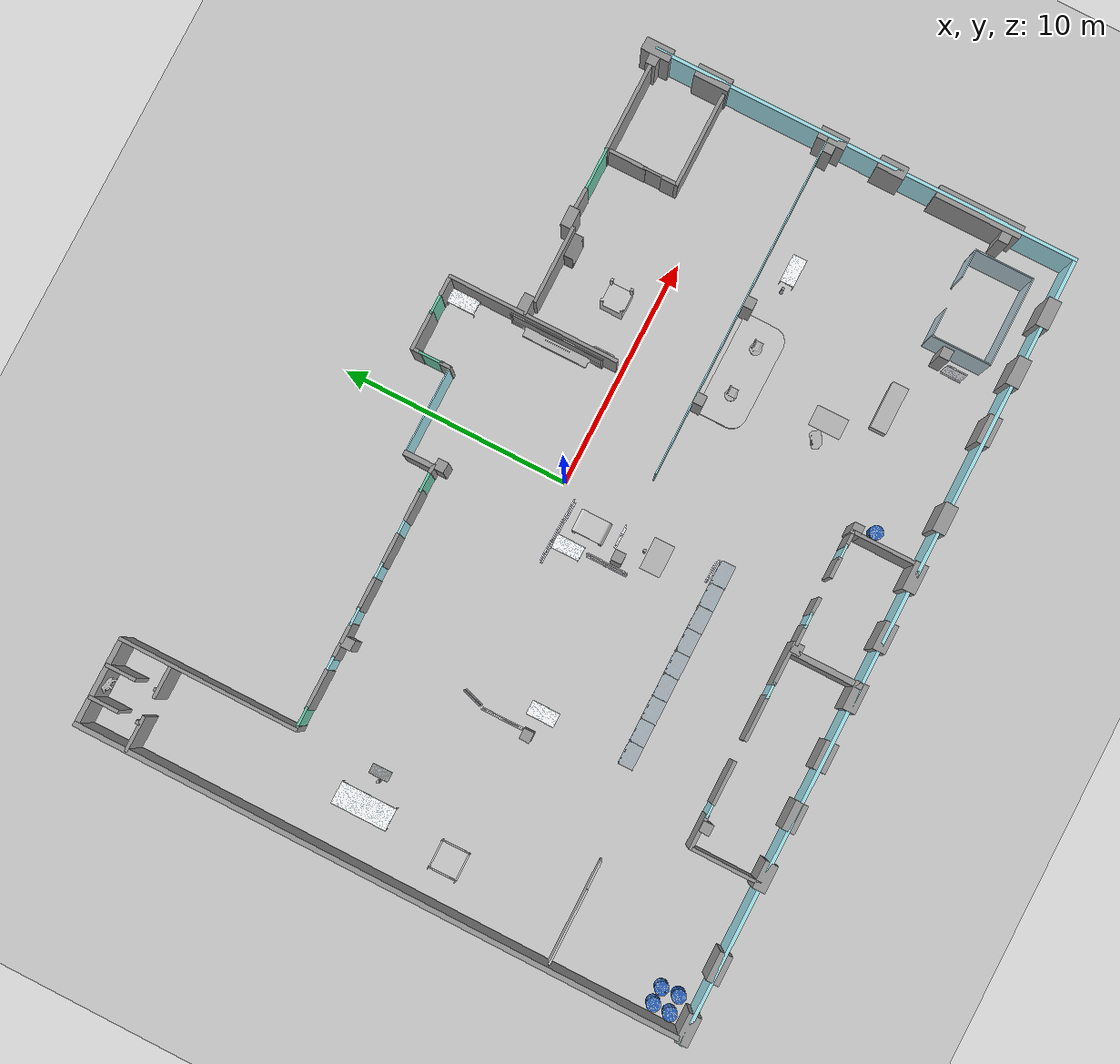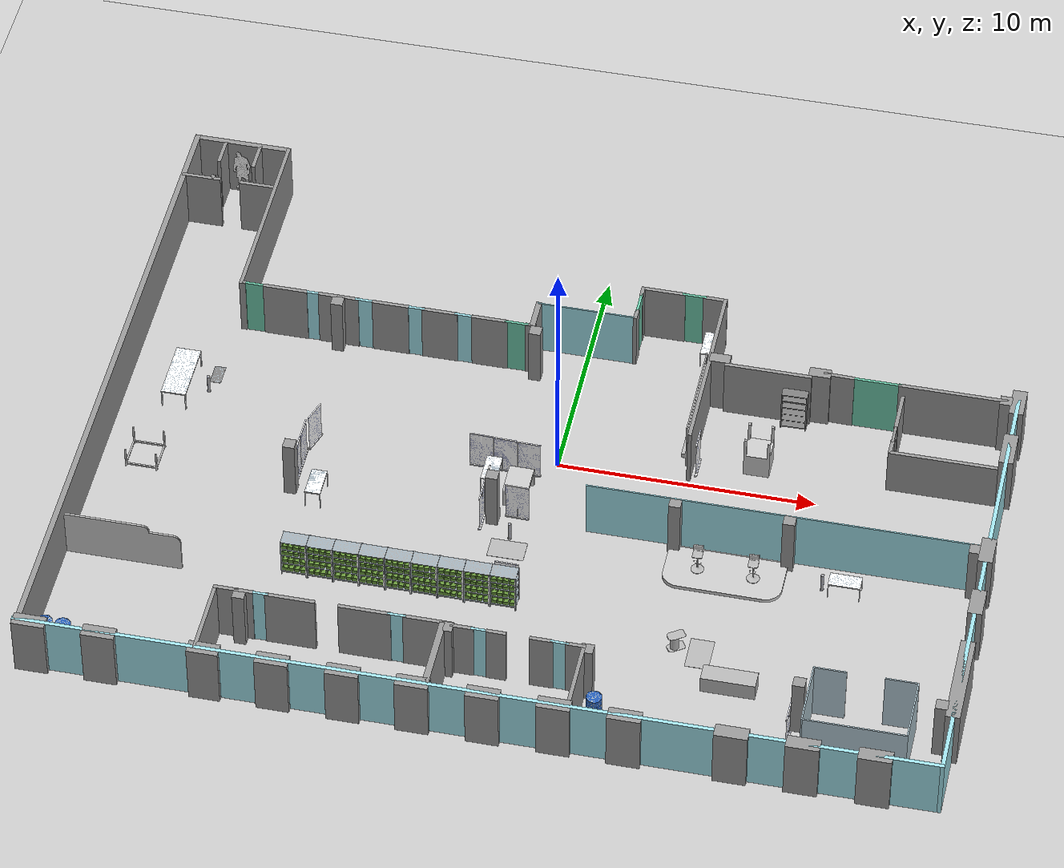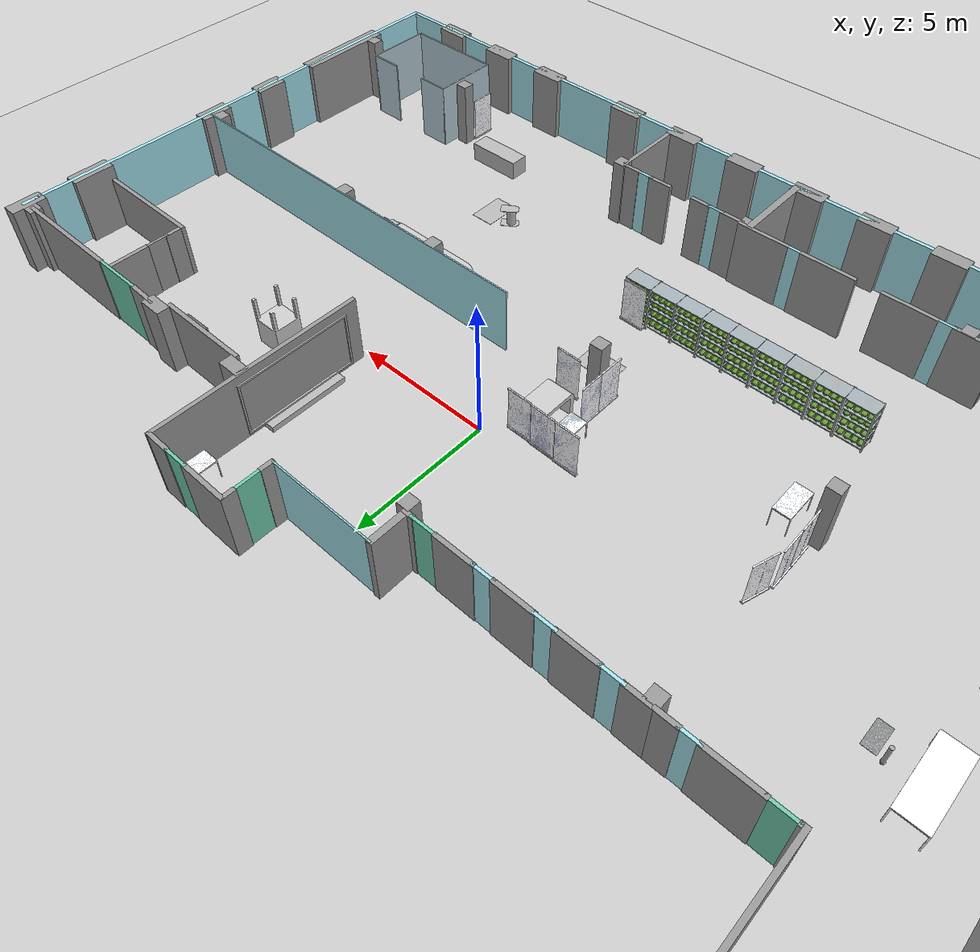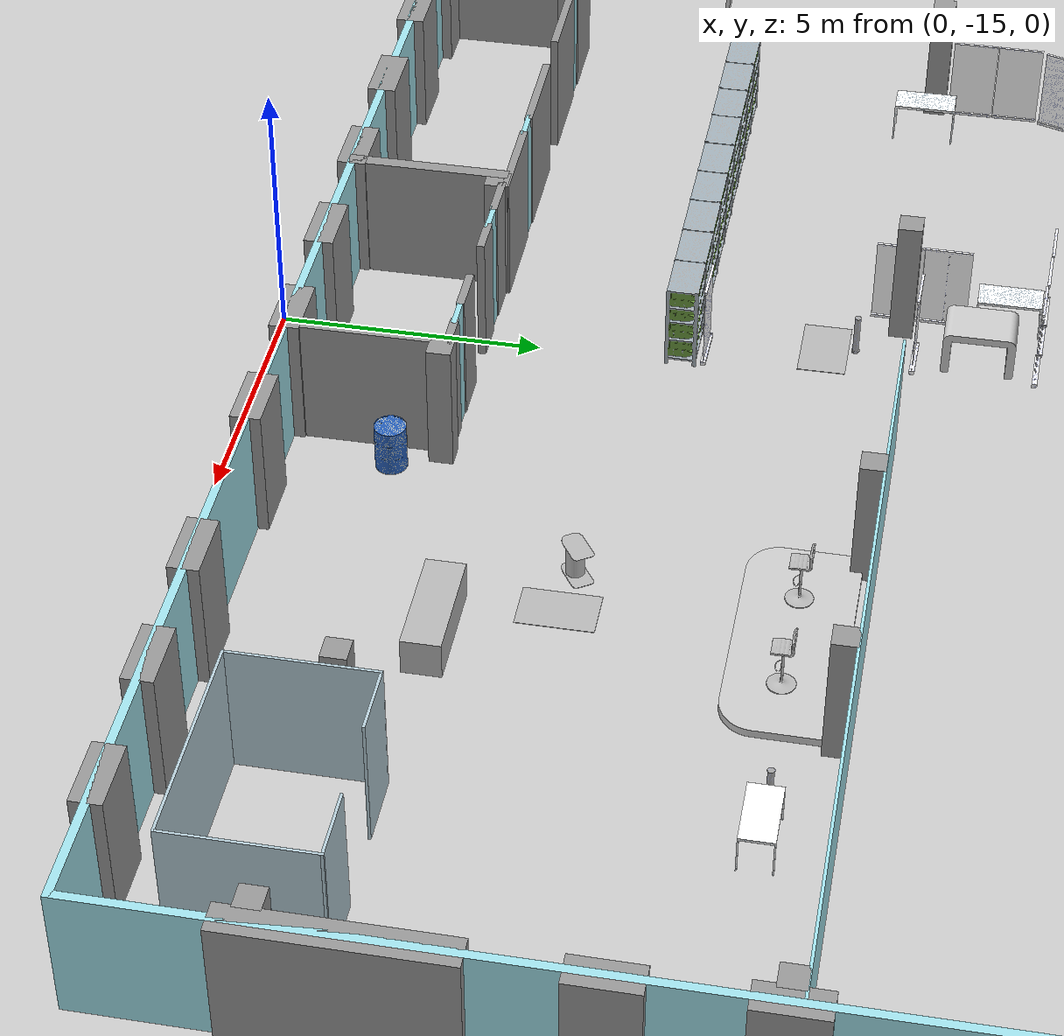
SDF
<sdf version="1.7">
 <world name="default">
  <plugin name="ros_link_attacher_plugin" filename="libgazebo_ros_link_attacher.so"/>
  <light name="sun" type="directional">
   <pose>0 0 10 0 -0 0</pose>
   <diffuse>0.8 0.8 0.8 1</diffuse>
   <specular>0.2 0.2 0.2 1</specular>
   <attenuation>
    <range>1000</range>
    <constant>0.9</constant>
    <linear>0.01</linear>
    <quadratic>0.001</quadratic>
   </attenuation>
   <direction>-0.5 0.1 -0.9</direction>
   <spot><inner_angle>0</inner_angle><outer_angle>0</outer_angle><falloff>0</falloff></spot>
  </light>
  <model name="ground_plane">
   <static>1</static>
   <link name="link">
    <collision name="collision">
     <geometry><plane><normal>0 0 1</normal><size>100 100</size></plane></geometry>
     <surface>
      <contact><collide_bitmask>65535</collide_bitmask></contact>
      <friction><ode><mu>100</mu><mu2>50</mu2></ode></friction>
     </surface>
    </collision>
    <visual name="visual">
     <cast_shadows>0</cast_shadows>
     <geometry><plane><normal>0 0 1</normal><size>100 100</size></plane></geometry>
     <material>
      <script><uri>file://media/materials/scripts/gazebo.material</uri><name>Gazebo/Grey</name></script>
     </material>
    </visual>
   </link>
  </model>
  <gravity>0 0 -9.8</gravity>
  <magnetic_field>6e-06 2.3e-05 -4.2e-05</magnetic_field>
  <atmosphere type="adiabatic"/>
  <physics name="default_physics" default="0" type="ode">
   <max_step_size>0.001</max_step_size>
   <real_time_factor>1</real_time_factor>
   <real_time_update_rate>1000</real_time_update_rate>
  </physics>
  <scene><ambient>0.4 0.4 0.4 1</ambient><background>0.7 0.7 0.7 1</background><shadows>1</shadows></scene>
  <audio><device>default</device></audio>
  <spherical_coordinates>
   <surface_model>EARTH_WGS84</surface_model>
   <latitude_deg>0</latitude_deg>
   <longitude_deg>0</longitude_deg>
   <elevation>0</elevation>
   <heading_deg>0</heading_deg>
  </spherical_coordinates>
  <model name="Pilotfabrik"><pose>-0.88371 -0.686599 0 0 -0 0</pose><static>1</static></model>
  <model name="Pilotfabrik_0"><pose>-0.936681 1.63881 0 0 -0 0</pose><static>1</static></model>
  <model name="PilotfabrikFinal">
   <pose>-0.137877 -0.8541 0 0 -0 0</pose>
   <link name="Wall_0">
    <collision name="Wall_0_Collision">
     <geometry><box><size>34.5 0.15 2.5</size></box></geometry>
     <pose>0 0 1.25 0 -0 0</pose>
    </collision>
    <visual name="Wall_0_Visual">
     <pose>0 0 1.25 0 -0 0</pose>
     <geometry><box><size>34.5 0.15 2.5</size></box></geometry>
     <material>
      <script><uri>file://media/materials/scripts/gazebo.material</uri><name>Gazebo/Grey</name></script>
      <ambient>0.639216 0.894118 0.933333 1</ambient>
     </material>
     <meta><layer>0</layer></meta>
    </visual>
    <pose>-0.104001 -13.1604 0 0 -0 0</pose>
   </link>
   <link name="Wall_10">
    <collision name="Wall_10_Collision">
     <geometry><box><size>1.25 0.55 2.5</size></box></geometry>
     <pose>0 0 1.25 0 -0 0</pose>
    </collision>
    <visual name="Wall_10_Visual">
     <pose>0 0 1.25 0 -0 0</pose>
     <geometry><box><size>1.25 0.55 2.5</size></box></geometry>
     <material>
      <script><uri>file://media/materials/scripts/gazebo.material</uri><name>Gazebo/Grey</name></script>
      <ambient>1 1 1 1</ambient>
     </material>
     <meta><layer>0</layer></meta>
    </visual>
    <pose>-7.557 -13.1635 0 0 -0 0</pose>
   </link>
   <link name="Wall_100">
    <collision name="Wall_100_Collision">
     <geometry><box><size>0.46 0.45 2.5</size></box></geometry>
     <pose>0 0 1.25 0 -0 0</pose>
    </collision>
    <visual name="Wall_100_Visual">
     <pose>0 0 1.25 0 -0 0</pose>
     <geometry><box><size>0.46 0.45 2.5</size></box></geometry>
     <material>
      <script><uri>file://media/materials/scripts/gazebo.material</uri><name>Gazebo/Grey</name></script>
      <ambient>1 1 1 1</ambient>
     </material>
     <meta><layer>0</layer></meta>
    </visual>
    <pose>16.6293 -2.47328 0 0 -0 0</pose>
   </link>
   <link name="Wall_104">
    <collision name="Wall_104_Collision">
     <geometry><box><size>26.82 0.22 2.5</size></box></geometry>
     <pose>0 0 1.25 0 -0 0</pose>
    </collision>
    <visual name="Wall_104_Visual">
     <pose>0 0 1.25 0 -0 0</pose>
     <geometry><box><size>26.82 0.22 2.5</size></box></geometry>
     <material>
      <script><uri>file://media/materials/scripts/gazebo.material</uri><name>Gazebo/Grey</name></script>
      <ambient>1 1 1 1</ambient>
     </material>
     <meta><layer>0</layer></meta>
    </visual>
    <pose>-17.1451 0.04188 0 0 -0 -1.5708</pose>
   </link>
   <link name="Wall_107">
    <collision name="Wall_107_Collision">
     <geometry><box><size>3.88877 0.22 2.5</size></box></geometry>
     <pose>0 0 1.25 0 -0 0</pose>
    </collision>
    <visual name="Wall_107_Visual">
     <pose>0 0 1.25 0 -0 0</pose>
     <geometry><box><size>3.88877 0.22 2.5</size></box></geometry>
     <material>
      <script><uri>file://media/materials/scripts/gazebo.material</uri><name>Gazebo/Grey</name></script>
      <ambient>1 1 1 1</ambient>
     </material>
     <meta><layer>0</layer></meta>
    </visual>
    <pose>-15.3107 13.337 0 0 -0 -0.002611</pose>
   </link>
   <link name="Wall_112">
    <collision name="Wall_112_Collision">
     <geometry><box><size>7.86266 0.15 2.5</size></box></geometry>
     <pose>0 0 1.25 0 -0 0</pose>
    </collision>
    <visual name="Wall_112_Visual">
     <pose>0 0 1.25 0 -0 0</pose>
     <geometry><box><size>7.86266 0.15 2.5</size></box></geometry>
     <material>
      <script><uri>file://media/materials/scripts/gazebo.material</uri><name>Gazebo/Grey</name></script>
      <ambient>1 1 1 1</ambient>
     </material>
     <meta><layer>0</layer></meta>
    </visual>
    <pose>-13.4151 9.50726 0 0 -0 1.5708</pose>
   </link>
   <link name="Wall_114">
    <collision name="Wall_114_Collision">
     <geometry><box><size>1.55074 0.15 2.5</size></box></geometry>
     <pose>0 0 1.25 0 -0 0</pose>
    </collision>
    <visual name="Wall_114_Visual">
     <pose>0 0 1.25 0 -0 0</pose>
     <geometry><box><size>1.55074 0.15 2.5</size></box></geometry>
     <material>
      <script><uri>file://media/materials/scripts/gazebo.material</uri><name>Gazebo/Grey</name></script>
      <ambient>1 1 1 1</ambient>
     </material>
     <meta><layer>0</layer></meta>
    </visual>
    <pose>-16.4215 11.1312 0 0 -0 3.14159</pose>
   </link>
   <link name="Wall_118">
    <collision name="Wall_118_Collision">
     <geometry><box><size>1.49886 0.15 2.5</size></box></geometry>
     <pose>0 0 1.25 0 -0 0</pose>
    </collision>
    <visual name="Wall_118_Visual">
     <pose>0 0 1.25 0 -0 0</pose>
     <geometry><box><size>1.49886 0.15 2.5</size></box></geometry>
     <material>
      <script><uri>file://media/materials/scripts/gazebo.material</uri><name>Gazebo/Grey</name></script>
      <ambient>1 1 1 1</ambient>
     </material>
     <meta><layer>0</layer></meta>
    </visual>
    <pose>-14.1216 11.1308 0 0 -0 0</pose>
   </link>
   <link name="Wall_12">
    <collision name="Wall_12_Collision">
     <geometry><box><size>1.25 0.55 2.5</size></box></geometry>
     <pose>0 0 1.25 0 -0 0</pose>
    </collision>
    <visual name="Wall_12_Visual">
     <pose>0 0 1.25 0 -0 0</pose>
     <geometry><box><size>1.25 0.55 2.5</size></box></geometry>
     <material>
      <script><uri>file://media/materials/scripts/gazebo.material</uri><name>Gazebo/Grey</name></script>
      <ambient>1 1 1 1</ambient>
     </material>
     <meta><layer>0</layer></meta>
    </visual>
    <pose>-4.92573 -13.1637 0 0 -0 0</pose>
   </link>
   <link name="Wall_120">
    <collision name="Wall_120_Collision">
     <geometry><box><size>1.30002 0.15 2.5</size></box></geometry>
     <pose>0 0 1.25 0 -0 0</pose>
    </collision>
    <visual name="Wall_120_Visual">
     <pose>0 0 1.25 0 -0 0</pose>
     <geometry><box><size>1.30002 0.15 2.5</size></box></geometry>
     <material>
      <script><uri>file://media/materials/scripts/gazebo.material</uri><name>Gazebo/Grey</name></script>
      <ambient>1 1 1 1</ambient>
     </material>
     <meta><layer>0</layer></meta>
    </visual>
    <pose>-15.9632 12.7608 0 0 -0 -1.5708</pose>
   </link>
   <link name="Wall_122">
    <collision name="Wall_122_Collision">
     <geometry><box><size>1.32606 0.15 2.5</size></box></geometry>
     <pose>0 0 1.25 0 -0 0</pose>
    </collision>
    <visual name="Wall_122_Visual">
     <pose>0 0 1.25 0 -0 0</pose>
     <geometry><box><size>1.32606 0.15 2.5</size></box></geometry>
     <material>
      <script><uri>file://media/materials/scripts/gazebo.material</uri><name>Gazebo/Grey</name></script>
      <ambient>1 1 1 1</ambient>
     </material>
     <meta><layer>0</layer></meta>
    </visual>
    <pose>-14.5625 12.7567 0 0 -0 1.5708</pose>
   </link>
   <link name="Wall_124">
    <collision name="Wall_124_Collision">
     <geometry><box><size>0.208 0.15 2.5</size></box></geometry>
     <pose>0 0 1.25 0 -0 0</pose>
    </collision>
    <visual name="Wall_124_Visual">
     <pose>0 0 1.25 0 -0 0</pose>
     <geometry><box><size>0.208 0.15 2.5</size></box></geometry>
     <material>
      <script><uri>file://media/materials/scripts/gazebo.material</uri><name>Gazebo/Grey</name></script>
      <ambient>1 1 1 1</ambient>
     </material>
     <meta><layer>0</layer></meta>
    </visual>
    <pose>-15.9753 11.2184 0 0 -0 -1.5708</pose>
   </link>
   <link name="Wall_129">
    <collision name="Wall_129_Collision">
     <geometry><box><size>0.229144 0.15 2.5</size></box></geometry>
     <pose>0 0 1.25 0 -0 0</pose>
    </collision>
    <visual name="Wall_129_Visual">
     <pose>0 0 1.25 0 -0 0</pose>
     <geometry><box><size>0.229144 0.15 2.5</size></box></geometry>
     <material>
      <script><uri>file://media/materials/scripts/gazebo.material</uri><name>Gazebo/Grey</name></script>
      <ambient>1 1 1 1</ambient>
     </material>
     <meta><layer>0</layer></meta>
    </visual>
    <pose>-14.5513 11.1805 0 0 -0 -1.5708</pose>
   </link>
   <link name="Wall_131">
    <collision name="Wall_131_Collision">
     <geometry><box><size>0.25 0.15 2.5</size></box></geometry>
     <pose>0 0 1.25 0 -0 0</pose>
    </collision>
    <visual name="Wall_131_Visual">
     <pose>0 0 1.25 0 -0 0</pose>
     <geometry><box><size>0.25 0.15 2.5</size></box></geometry>
     <material>
      <script><uri>file://media/materials/scripts/gazebo.material</uri><name>Gazebo/Grey</name></script>
      <ambient>1 1 1 1</ambient>
     </material>
     <meta><layer>0</layer></meta>
    </visual>
    <pose>-13.3651 5.65076 0 0 -0 0</pose>
   </link>
   <link name="Wall_132">
    <collision name="Wall_132_Collision">
     <geometry><box><size>0.95 0.1 2.5</size></box></geometry>
     <pose>0 0 1.25 0 -0 0</pose>
    </collision>
    <visual name="Wall_132_Visual">
     <pose>0 0 1.25 0 -0 0</pose>
     <geometry><box><size>0.95 0.1 2.5</size></box></geometry>
     <material>
      <script><uri>file://media/materials/scripts/gazebo.material</uri><name>Gazebo/Grey</name></script>
      <ambient>0.435294 0.796078 0.67451 1</ambient>
     </material>
     <meta><layer>0</layer></meta>
    </visual>
    <pose>-12.8901 5.65076 0 0 -0 0</pose>
   </link>
   <link name="Wall_133">
    <collision name="Wall_133_Collision">
     <geometry><box><size>1.75 0.15 2.5</size></box></geometry>
     <pose>0 0 1.25 0 -0 0</pose>
    </collision>
    <visual name="Wall_133_Visual">
     <pose>0 0 1.25 0 -0 0</pose>
     <geometry><box><size>1.75 0.15 2.5</size></box></geometry>
     <material>
      <script><uri>file://media/materials/scripts/gazebo.material</uri><name>Gazebo/Grey</name></script>
      <ambient>1 1 1 1</ambient>
     </material>
     <meta><layer>0</layer></meta>
    </visual>
    <pose>-11.6651 5.65076 0 0 -0 0</pose>
   </link>
   <link name="Wall_134">
    <collision name="Wall_134_Collision">
     <geometry><box><size>0.7 0.1 2.5</size></box></geometry>
     <pose>0 0 1.25 0 -0 0</pose>
    </collision>
    <visual name="Wall_134_Visual">
     <pose>0 0 1.25 0 -0 0</pose>
     <geometry><box><size>0.7 0.1 2.5</size></box></geometry>
     <material>
      <script><uri>file://media/materials/scripts/gazebo.material</uri><name>Gazebo/Grey</name></script>
      <ambient>0.639216 0.894118 0.933333 1</ambient>
     </material>
     <meta><layer>0</layer></meta>
    </visual>
    <pose>-10.5651 5.65076 0 0 -0 0</pose>
   </link>
   <link name="Wall_135">
    <collision name="Wall_135_Collision">
     <geometry><box><size>0.75 0.15 2.5</size></box></geometry>
     <pose>0 0 1.25 0 -0 0</pose>
    </collision>
    <visual name="Wall_135_Visual">
     <pose>0 0 1.25 0 -0 0</pose>
     <geometry><box><size>0.75 0.15 2.5</size></box></geometry>
     <material>
      <script><uri>file://media/materials/scripts/gazebo.material</uri><name>Gazebo/Grey</name></script>
      <ambient>1 1 1 1</ambient>
     </material>
     <meta><layer>0</layer></meta>
    </visual>
    <pose>-9.9651 5.65076 0 0 -0 0</pose>
   </link>
   <link name="Wall_137">
    <collision name="Wall_137_Collision">
     <geometry><box><size>0.46 0.45 2.5</size></box></geometry>
     <pose>0 0 1.25 0 -0 0</pose>
    </collision>
    <visual name="Wall_137_Visual">
     <pose>0 0 1.25 0 -0 0</pose>
     <geometry><box><size>0.46 0.45 2.5</size></box></geometry>
     <material>
      <script><uri>file://media/materials/scripts/gazebo.material</uri><name>Gazebo/Grey</name></script>
      <ambient>1 1 1 1</ambient>
     </material>
     <meta><layer>0</layer></meta>
    </visual>
    <pose>-9.51967 5.39926 0 0 -0 3.14159</pose>
   </link>
   <link name="Wall_14">
    <collision name="Wall_14_Collision">
     <geometry><box><size>1.25 0.55 2.5</size></box></geometry>
     <pose>0 0 1.25 0 -0 0</pose>
    </collision>
    <visual name="Wall_14_Visual">
     <pose>0 0 1.25 0 -0 0</pose>
     <geometry><box><size>1.25 0.55 2.5</size></box></geometry>
     <material>
      <script><uri>file://media/materials/scripts/gazebo.material</uri><name>Gazebo/Grey</name></script>
      <ambient>1 1 1 1</ambient>
     </material>
     <meta><layer>0</layer></meta>
    </visual>
    <pose>-2.33348 -13.1639 0 0 -0 0</pose>
   </link>
   <link name="Wall_151">
    <collision name="Wall_151_Collision">
     <geometry><box><size>0.400151 0.15 2.5</size></box></geometry>
     <pose>0 0 1.25 0 -0 0</pose>
    </collision>
    <visual name="Wall_151_Visual">
     <pose>0 0 1.25 0 -0 0</pose>
     <geometry><box><size>0.400151 0.15 2.5</size></box></geometry>
     <material>
      <script><uri>file://media/materials/scripts/gazebo.material</uri><name>Gazebo/Grey</name></script>
      <ambient>1 1 1 1</ambient>
     </material>
     <meta><layer>0</layer></meta>
    </visual>
    <pose>-1.94085 5.65194 0 0 -0 -3.1401</pose>
   </link>
   <link name="Wall_152">
    <collision name="Wall_152_Collision">
     <geometry><box><size>0.949637 0.1 2.5</size></box></geometry>
     <pose>0 0 1.25 0 -0 0</pose>
    </collision>
    <visual name="Wall_152_Visual">
     <pose>0 0 1.25 0 -0 0</pose>
     <geometry><box><size>0.949637 0.1 2.5</size></box></geometry>
     <material>
      <script><uri>file://media/materials/scripts/gazebo.material</uri><name>Gazebo/Grey</name></script>
      <ambient>0.435294 0.796078 0.67451 1</ambient>
     </material>
     <meta><layer>0</layer></meta>
    </visual>
    <pose>-2.4911 5.65176 0 0 -0 3.14159</pose>
   </link>
   <link name="Wall_153">
    <collision name="Wall_153_Collision">
     <geometry><box><size>1.41491 0.15 2.5</size></box></geometry>
     <pose>0 0 1.25 0 -0 0</pose>
    </collision>
    <visual name="Wall_153_Visual">
     <pose>0 0 1.25 0 -0 0</pose>
     <geometry><box><size>1.41491 0.15 2.5</size></box></geometry>
     <material>
      <script><uri>file://media/materials/scripts/gazebo.material</uri><name>Gazebo/Grey</name></script>
      <ambient>1 1 1 1</ambient>
     </material>
     <meta><layer>0</layer></meta>
    </visual>
    <pose>-3.5486 5.65176 0 0 -0 3.14159</pose>
   </link>
   <link name="Wall_154">
    <collision name="Wall_154_Collision">
     <geometry><box><size>0.80452 0.1 2.5</size></box></geometry>
     <pose>0 0 1.25 0 -0 0</pose>
    </collision>
    <visual name="Wall_154_Visual">
     <pose>0 0 1.25 0 -0 0</pose>
     <geometry><box><size>0.80452 0.1 2.5</size></box></geometry>
     <material>
      <script><uri>file://media/materials/scripts/gazebo.material</uri><name>Gazebo/Grey</name></script>
      <ambient>0.639216 0.894118 0.933333 1</ambient>
     </material>
     <meta><layer>0</layer></meta>
    </visual>
    <pose>-4.5336 5.65176 0 0 -0 3.14159</pose>
   </link>
   <link name="Wall_155">
    <collision name="Wall_155_Collision">
     <geometry><box><size>1.41781 0.15 2.5</size></box></geometry>
     <pose>0 0 1.25 0 -0 0</pose>
    </collision>
    <visual name="Wall_155_Visual">
     <pose>0 0 1.25 0 -0 0</pose>
     <geometry><box><size>1.41781 0.15 2.5</size></box></geometry>
     <material>
      <script><uri>file://media/materials/scripts/gazebo.material</uri><name>Gazebo/Grey</name></script>
      <ambient>1 1 1 1</ambient>
     </material>
     <meta><layer>0</layer></meta>
    </visual>
    <pose>-5.5196 5.65176 0 0 -0 3.14159</pose>
   </link>
   <link name="Wall_156">
    <collision name="Wall_156_Collision">
     <geometry><box><size>0.776875 0.1 2.5</size></box></geometry>
     <pose>0 0 1.25 0 -0 0</pose>
    </collision>
    <visual name="Wall_156_Visual">
     <pose>0 0 1.25 0 -0 0</pose>
     <geometry><box><size>0.776875 0.1 2.5</size></box></geometry>
     <material>
      <script><uri>file://media/materials/scripts/gazebo.material</uri><name>Gazebo/Grey</name></script>
      <ambient>0.639216 0.894118 0.933333 1</ambient>
     </material>
     <meta><layer>0</layer></meta>
    </visual>
    <pose>-6.4916 5.65176 0 0 -0 3.14159</pose>
   </link>
   <link name="Wall_157">
    <collision name="Wall_157_Collision">
     <geometry><box><size>1.43813 0.15 2.5</size></box></geometry>
     <pose>0 0 1.25 0 -0 0</pose>
    </collision>
    <visual name="Wall_157_Visual">
     <pose>0 0 1.25 0 -0 0</pose>
     <geometry><box><size>1.43813 0.15 2.5</size></box></geometry>
     <material>
      <script><uri>file://media/materials/scripts/gazebo.material</uri><name>Gazebo/Grey</name></script>
      <ambient>1 1 1 1</ambient>
     </material>
     <meta><layer>0</layer></meta>
    </visual>
    <pose>-7.4741 5.65076 0 0 -0 -3.14004</pose>
   </link>
   <link name="Wall_158">
    <collision name="Wall_158_Collision">
     <geometry><box><size>0.798853 0.1 2.5</size></box></geometry>
     <pose>0 0 1.25 0 -0 0</pose>
    </collision>
    <visual name="Wall_158_Visual">
     <pose>0 0 1.25 0 -0 0</pose>
     <geometry><box><size>0.798853 0.1 2.5</size></box></geometry>
     <material>
      <script><uri>file://media/materials/scripts/gazebo.material</uri><name>Gazebo/Grey</name></script>
      <ambient>0.639216 0.894118 0.933333 1</ambient>
     </material>
     <meta><layer>0</layer></meta>
    </visual>
    <pose>-8.4676 5.64976 0 0 -0 3.14159</pose>
   </link>
   <link name="Wall_159">
    <collision name="Wall_159_Collision">
     <geometry><box><size>0.908853 0.15 2.5</size></box></geometry>
     <pose>0 0 1.25 0 -0 0</pose>
    </collision>
    <visual name="Wall_159_Visual">
     <pose>0 0 1.25 0 -0 0</pose>
     <geometry><box><size>0.908853 0.15 2.5</size></box></geometry>
     <material>
      <script><uri>file://media/materials/scripts/gazebo.material</uri><name>Gazebo/Grey</name></script>
      <ambient>1 1 1 1</ambient>
     </material>
     <meta><layer>0</layer></meta>
    </visual>
    <pose>-9.19653 5.65094 0 0 -0 3.13847</pose>
   </link>
   <link name="Wall_16">
    <collision name="Wall_16_Collision">
     <geometry><box><size>1.25 0.55 2.5</size></box></geometry>
     <pose>0 0 1.25 0 -0 0</pose>
    </collision>
    <visual name="Wall_16_Visual">
     <pose>0 0 1.25 0 -0 0</pose>
     <geometry><box><size>1.25 0.55 2.5</size></box></geometry>
     <material>
      <script><uri>file://media/materials/scripts/gazebo.material</uri><name>Gazebo/Grey</name></script>
      <ambient>1 1 1 1</ambient>
     </material>
     <meta><layer>0</layer></meta>
    </visual>
    <pose>0.284996 -13.1635 0 0 -0 0</pose>
   </link>
   <link name="Wall_161">
    <collision name="Wall_161_Collision">
     <geometry><box><size>0.46 0.45 2.5</size></box></geometry>
     <pose>0 0 1.25 0 -0 0</pose>
    </collision>
    <visual name="Wall_161_Visual">
     <pose>0 0 1.25 0 -0 0</pose>
     <geometry><box><size>0.46 0.45 2.5</size></box></geometry>
     <material>
      <script><uri>file://media/materials/scripts/gazebo.material</uri><name>Gazebo/Grey</name></script>
      <ambient>1 1 1 1</ambient>
     </material>
     <meta><layer>0</layer></meta>
    </visual>
    <pose>-1.67836 5.39095 0 0 -0 0</pose>
   </link>
   <link name="Wall_167">
    <collision name="Wall_167_Collision">
     <geometry><box><size>1.3 0.22 2.5</size></box></geometry>
     <pose>0 0 1.25 0 -0 0</pose>
    </collision>
    <visual name="Wall_167_Visual">
     <pose>0 0 1.25 0 -0 0</pose>
     <geometry><box><size>1.3 0.22 2.5</size></box></geometry>
     <material>
      <script><uri>file://media/materials/scripts/gazebo.material</uri><name>Gazebo/Grey</name></script>
      <ambient>1 1 1 1</ambient>
     </material>
     <meta><layer>0</layer></meta>
    </visual>
    <pose>-1.86149 6.29053 0 0 -0 -1.5708</pose>
   </link>
   <link name="Wall_170">
    <collision name="Wall_170_Collision">
     <geometry><box><size>3.881 0.05 2.5</size></box></geometry>
     <pose>0 0 1.25 0 -0 0</pose>
    </collision>
    <visual name="Wall_170_Visual">
     <pose>0 0 1.25 0 -0 0</pose>
     <geometry><box><size>3.881 0.05 2.5</size></box></geometry>
     <material>
      <script><uri>file://media/materials/scripts/gazebo.material</uri><name>Gazebo/Grey</name></script>
      <ambient>0.639216 0.894118 0.933333 1</ambient>
     </material>
     <meta><layer>0</layer></meta>
    </visual>
    <pose>0.034396 6.88376 0 0 -0 3.14159</pose>
   </link>
   <link name="Wall_177">
    <collision name="Wall_177_Collision">
     <geometry><box><size>0.5 0.15 2.5</size></box></geometry>
     <pose>0 0 1.25 0 -0 0</pose>
    </collision>
    <visual name="Wall_177_Visual">
     <pose>0 0 1.25 0 -0 0</pose>
     <geometry><box><size>0.5 0.15 2.5</size></box></geometry>
     <material>
      <script><uri>file://media/materials/scripts/gazebo.material</uri><name>Gazebo/Grey</name></script>
      <ambient>1 1 1 1</ambient>
     </material>
     <meta><layer>0</layer></meta>
    </visual>
    <pose>1.93271 8.36389 0 0 -0 -1.56972</pose>
   </link>
   <link name="Wall_178">
    <collision name="Wall_178_Collision">
     <geometry><box><size>1.05242 0.1 2.5</size></box></geometry>
     <pose>0 0 1.25 0 -0 0</pose>
    </collision>
    <visual name="Wall_178_Visual">
     <pose>0 0 1.25 0 -0 0</pose>
     <geometry><box><size>1.05242 0.1 2.5</size></box></geometry>
     <material>
      <script><uri>file://media/materials/scripts/gazebo.material</uri><name>Gazebo/Grey</name></script>
      <ambient>0.435294 0.796078 0.67451 1</ambient>
     </material>
     <meta><layer>0</layer></meta>
    </visual>
    <pose>1.9354 7.71276 0 0 -0 -1.56554</pose>
   </link>
   <link name="Wall_179">
    <collision name="Wall_179_Collision">
     <geometry><box><size>0.484309 0.15 2.5</size></box></geometry>
     <pose>0 0 1.25 0 -0 0</pose>
    </collision>
    <visual name="Wall_179_Visual">
     <pose>0 0 1.25 0 -0 0</pose>
     <geometry><box><size>0.484309 0.15 2.5</size></box></geometry>
     <material>
      <script><uri>file://media/materials/scripts/gazebo.material</uri><name>Gazebo/Grey</name></script>
      <ambient>1 1 1 1</ambient>
     </material>
     <meta><layer>0</layer></meta>
    </visual>
    <pose>1.93521 7.06941 0 0 -0 -1.58686</pose>
   </link>
   <link name="Wall_18">
    <collision name="Wall_18_Collision">
     <geometry><box><size>1.25 0.55 2.5</size></box></geometry>
     <pose>0 0 1.25 0 -0 0</pose>
    </collision>
    <visual name="Wall_18_Visual">
     <pose>0 0 1.25 0 -0 0</pose>
     <geometry><box><size>1.25 0.55 2.5</size></box></geometry>
     <material>
      <script><uri>file://media/materials/scripts/gazebo.material</uri><name>Gazebo/Grey</name></script>
      <ambient>1 1 1 1</ambient>
     </material>
     <meta><layer>0</layer></meta>
    </visual>
    <pose>2.90382 -13.1499 0 0 -0 0</pose>
   </link>
   <link name="Wall_181">
    <collision name="Wall_181_Collision">
     <geometry><box><size>1.75 0.15 2.5</size></box></geometry>
     <pose>0 0 1.25 0 -0 0</pose>
    </collision>
    <visual name="Wall_181_Visual">
     <pose>0 0 1.25 0 -0 0</pose>
     <geometry><box><size>1.75 0.15 2.5</size></box></geometry>
     <material>
      <script><uri>file://media/materials/scripts/gazebo.material</uri><name>Gazebo/Grey</name></script>
      <ambient>1 1 1 1</ambient>
     </material>
     <meta><layer>0</layer></meta>
    </visual>
    <pose>2.73271 8.53889 0 0 -0 -0.000167</pose>
   </link>
   <link name="Wall_182">
    <collision name="Wall_182_Collision">
     <geometry><box><size>0.949624 0.1 2.5</size></box></geometry>
     <pose>0 0 1.25 0 -0 0</pose>
    </collision>
    <visual name="Wall_182_Visual">
     <pose>0 0 1.25 0 -0 0</pose>
     <geometry><box><size>0.949624 0.1 2.5</size></box></geometry>
     <material>
      <script><uri>file://media/materials/scripts/gazebo.material</uri><name>Gazebo/Grey</name></script>
      <ambient>0.435294 0.796078 0.67451 1</ambient>
     </material>
     <meta><layer>0</layer></meta>
    </visual>
    <pose>3.9579 8.53876 0 0 -0 0</pose>
   </link>
   <link name="Wall_183">
    <collision name="Wall_183_Collision">
     <geometry><box><size>0.934401 0.15 2.5</size></box></geometry>
     <pose>0 0 1.25 0 -0 0</pose>
    </collision>
    <visual name="Wall_183_Visual">
     <pose>0 0 1.25 0 -0 0</pose>
     <geometry><box><size>0.934401 0.15 2.5</size></box></geometry>
     <material>
      <script><uri>file://media/materials/scripts/gazebo.material</uri><name>Gazebo/Grey</name></script>
      <ambient>1 1 1 1</ambient>
     </material>
     <meta><layer>0</layer></meta>
    </visual>
    <pose>4.7749 8.53326 0 0 -0 -0.01403</pose>
   </link>
   <link name="Wall_186">
    <collision name="Wall_186_Collision">
     <geometry><box><size>7.5 0.15 2.5</size></box></geometry>
     <pose>0 0 1.25 0 -0 0</pose>
    </collision>
    <visual name="Wall_186_Visual">
     <pose>0 0 1.25 0 -0 0</pose>
     <geometry><box><size>7.5 0.15 2.5</size></box></geometry>
     <material>
      <script><uri>file://media/materials/scripts/gazebo.material</uri><name>Gazebo/Grey</name></script>
      <ambient>1 1 1 1</ambient>
     </material>
     <meta><layer>0</layer></meta>
    </visual>
    <pose>5.1669 4.85276 0 0 -0 -1.5708</pose>
   </link>
   <link name="Wall_188">
    <collision name="Wall_188_Collision">
     <geometry><box><size>0.8 0.45 2.5</size></box></geometry>
     <pose>0 0 1.25 0 -0 0</pose>
    </collision>
    <visual name="Wall_188_Visual">
     <pose>0 0 1.25 0 -0 0</pose>
     <geometry><box><size>0.8 0.45 2.5</size></box></geometry>
     <material>
      <script><uri>file://media/materials/scripts/gazebo.material</uri><name>Gazebo/Grey</name></script>
      <ambient>1 1 1 1</ambient>
     </material>
     <meta><layer>0</layer></meta>
    </visual>
    <pose>5.54638 5.39249 0 0 -0 3.14159</pose>
   </link>
   <link name="Wall_190">
    <collision name="Wall_190_Collision">
     <geometry><box><size>0.85 0.45 2.5</size></box></geometry>
     <pose>0 0 1.25 0 -0 0</pose>
    </collision>
    <visual name="Wall_190_Visual">
     <pose>0 0 1.25 0 -0 0</pose>
     <geometry><box><size>0.85 0.45 2.5</size></box></geometry>
     <material>
      <script><uri>file://media/materials/scripts/gazebo.material</uri><name>Gazebo/Grey</name></script>
      <ambient>1 1 1 1</ambient>
     </material>
     <meta><layer>0</layer></meta>
    </visual>
    <pose>9.43474 5.39984 0 0 -0 0</pose>
   </link>
   <link name="Wall_193">
    <collision name="Wall_193_Collision">
     <geometry><box><size>3.37976 0.15 2.5</size></box></geometry>
     <pose>0 0 1.25 0 -0 0</pose>
    </collision>
    <visual name="Wall_193_Visual">
     <pose>0 0 1.25 0 -0 0</pose>
     <geometry><box><size>3.37976 0.15 2.5</size></box></geometry>
     <material>
      <script><uri>file://media/materials/scripts/gazebo.material</uri><name>Gazebo/Grey</name></script>
      <ambient>1 1 1 1</ambient>
     </material>
     <meta><layer>0</layer></meta>
    </visual>
    <pose>7.46601 5.10548 0 0 -0 0</pose>
   </link>
   <link name="Wall_195">
    <collision name="Wall_195_Collision">
     <geometry><box><size>4.21976 0.15 2.5</size></box></geometry>
     <pose>0 0 1.25 0 -0 0</pose>
    </collision>
    <visual name="Wall_195_Visual">
     <pose>0 0 1.25 0 -0 0</pose>
     <geometry><box><size>4.21976 0.15 2.5</size></box></geometry>
     <material>
      <script><uri>file://media/materials/scripts/gazebo.material</uri><name>Gazebo/Grey</name></script>
      <ambient>1 1 1 1</ambient>
     </material>
     <meta><layer>0</layer></meta>
    </visual>
    <pose>14.5838 5.37073 0 0 -0 -1.2e-05</pose>
   </link>
   <link name="Wall_197">
    <collision name="Wall_197_Collision">
     <geometry><box><size>0.46 0.45 2.5</size></box></geometry>
     <pose>0 0 1.25 0 -0 0</pose>
    </collision>
    <visual name="Wall_197_Visual">
     <pose>0 0 1.25 0 -0 0</pose>
     <geometry><box><size>0.46 0.45 2.5</size></box></geometry>
     <material>
      <script><uri>file://media/materials/scripts/gazebo.material</uri><name>Gazebo/Grey</name></script>
      <ambient>1 1 1 1</ambient>
     </material>
     <meta><layer>0</layer></meta>
    </visual>
    <pose>16.6074 5.38554 0 0 -0 0</pose>
   </link>
   <link name="Wall_199">
    <collision name="Wall_199_Collision">
     <geometry><box><size>1.94999 0.1 2.5</size></box></geometry>
     <pose>0 0 1.25 0 -0 0</pose>
    </collision>
    <visual name="Wall_199_Visual">
     <pose>0 0 1.25 0 -0 0</pose>
     <geometry><box><size>1.94999 0.1 2.5</size></box></geometry>
     <material>
      <script><uri>file://media/materials/scripts/gazebo.material</uri><name>Gazebo/Grey</name></script>
      <ambient>0.435294 0.796078 0.67451 1</ambient>
     </material>
     <meta><layer>0</layer></meta>
    </visual>
    <pose>11.6239 5.37076 0 0 -0 3.14159</pose>
   </link>
   <link name="Wall_2">
    <collision name="Wall_2_Collision">
     <geometry><box><size>1.25 0.55 2.5</size></box></geometry>
     <pose>0 0 1.25 0 -0 0</pose>
    </collision>
    <visual name="Wall_2_Visual">
     <pose>0 0 1.25 0 -0 0</pose>
     <geometry><box><size>1.25 0.55 2.5</size></box></geometry>
     <material>
      <script><uri>file://media/materials/scripts/gazebo.material</uri><name>Gazebo/Grey</name></script>
      <ambient>1 1 1 1</ambient>
     </material>
     <meta><layer>0</layer></meta>
    </visual>
    <pose>-16.6961 -13.1632 0 0 -0 0</pose>
   </link>
   <link name="Wall_20">
    <collision name="Wall_20_Collision">
     <geometry><box><size>1.25 0.55 2.5</size></box></geometry>
     <pose>0 0 1.25 0 -0 0</pose>
    </collision>
    <visual name="Wall_20_Visual">
     <pose>0 0 1.25 0 -0 0</pose>
     <geometry><box><size>1.25 0.55 2.5</size></box></geometry>
     <material>
      <script><uri>file://media/materials/scripts/gazebo.material</uri><name>Gazebo/Grey</name></script>
      <ambient>1 1 1 1</ambient>
     </material>
     <meta><layer>0</layer></meta>
    </visual>
    <pose>5.5089 -13.1632 0 0 -0 0</pose>
   </link>
   <link name="Wall_200">
    <collision name="Wall_200_Collision">
     <geometry><box><size>1.21455 0.15 2.5</size></box></geometry>
     <pose>0 0 1.25 0 -0 0</pose>
    </collision>
    <visual name="Wall_200_Visual">
     <pose>0 0 1.25 0 -0 0</pose>
     <geometry><box><size>1.21455 0.15 2.5</size></box></geometry>
     <material>
      <script><uri>file://media/materials/scripts/gazebo.material</uri><name>Gazebo/Grey</name></script>
      <ambient>1 1 1 1</ambient>
     </material>
     <meta><layer>0</layer></meta>
    </visual>
    <pose>10.1668 5.3853 0 0 -0 3.11427</pose>
   </link>
   <link name="Wall_204">
    <collision name="Wall_204_Collision">
     <geometry><box><size>0.75 0.15 2</size></box></geometry>
     <pose>0 0 1 0 -0 0</pose>
    </collision>
    <visual name="Wall_204_Visual">
     <pose>0 0 1 0 -0 0</pose>
     <geometry><box><size>0.75 0.15 2</size></box></geometry>
     <material>
      <script><uri>file://media/materials/scripts/gazebo.material</uri><name>Gazebo/Grey</name></script>
      <ambient>1 1 1 1</ambient>
     </material>
     <meta><layer>0</layer></meta>
    </visual>
    <pose>12.6699 2.57676 0 0 -0 1.5708</pose>
   </link>
   <link name="Wall_206">
    <collision name="Wall_206_Collision">
     <geometry><box><size>4.25 0.15 2</size></box></geometry>
     <pose>0 0 1 0 -0 0</pose>
    </collision>
    <visual name="Wall_206_Visual">
     <pose>0 0 1 0 -0 0</pose>
     <geometry><box><size>4.25 0.15 2</size></box></geometry>
     <material>
      <script><uri>file://media/materials/scripts/gazebo.material</uri><name>Gazebo/Grey</name></script>
      <ambient>1 1 1 1</ambient>
     </material>
     <meta><layer>0</layer></meta>
    </visual>
    <pose>14.7199 2.27676 0 0 -0 0</pose>
   </link>
   <link name="Wall_208">
    <collision name="Wall_208_Collision">
     <geometry><box><size>0.95 0.1 2</size></box></geometry>
     <pose>0 0 1 0 -0 0</pose>
    </collision>
    <visual name="Wall_208_Visual">
     <pose>0 0 1 0 -0 0</pose>
     <geometry><box><size>0.95 0.1 2</size></box></geometry>
     <material>
      <script><uri>file://media/materials/scripts/gazebo.material</uri><name>Gazebo/Grey</name></script>
      <ambient>1 1 1 1</ambient>
     </material>
     <meta><layer>0</layer></meta>
    </visual>
    <pose>12.6699 3.30176 0 0 -0 1.5708</pose>
   </link>
   <link name="Wall_209">
    <collision name="Wall_209_Collision">
     <geometry><box><size>1.75 0.15 2</size></box></geometry>
     <pose>0 0 1 0 -0 0</pose>
    </collision>
    <visual name="Wall_209_Visual">
     <pose>0 0 1 0 -0 0</pose>
     <geometry><box><size>1.75 0.15 2</size></box></geometry>
     <material>
      <script><uri>file://media/materials/scripts/gazebo.material</uri><name>Gazebo/Grey</name></script>
      <ambient>1 1 1 1</ambient>
     </material>
     <meta><layer>0</layer></meta>
    </visual>
    <pose>12.6699 4.52676 0 0 -0 1.5708</pose>
   </link>
   <link name="Wall_22">
    <collision name="Wall_22_Collision">
     <geometry><box><size>1.25 0.55 2.5</size></box></geometry>
     <pose>0 0 1.25 0 -0 0</pose>
    </collision>
    <visual name="Wall_22_Visual">
     <pose>0 0 1.25 0 -0 0</pose>
     <geometry><box><size>1.25 0.55 2.5</size></box></geometry>
     <material>
      <script><uri>file://media/materials/scripts/gazebo.material</uri><name>Gazebo/Grey</name></script>
      <ambient>1 1 1 1</ambient>
     </material>
     <meta><layer>0</layer></meta>
    </visual>
    <pose>9.41709 -13.1559 0 0 -0 0</pose>
   </link>
   <link name="Wall_24">
    <collision name="Wall_24_Collision">
     <geometry><box><size>1.25 0.55 2.5</size></box></geometry>
     <pose>0 0 1.25 0 -0 0</pose>
    </collision>
    <visual name="Wall_24_Visual">
     <pose>0 0 1.25 0 -0 0</pose>
     <geometry><box><size>1.25 0.55 2.5</size></box></geometry>
     <material>
      <script><uri>file://media/materials/scripts/gazebo.material</uri><name>Gazebo/Grey</name></script>
      <ambient>1 1 1 1</ambient>
     </material>
     <meta><layer>0</layer></meta>
    </visual>
    <pose>12.0229 -13.1503 0 0 -0 0</pose>
   </link>
   <link name="Wall_26">
    <collision name="Wall_26_Collision">
     <geometry><box><size>1.25 0.55 2.5</size></box></geometry>
     <pose>0 0 1.25 0 -0 0</pose>
    </collision>
    <visual name="Wall_26_Visual">
     <pose>0 0 1.25 0 -0 0</pose>
     <geometry><box><size>1.25 0.55 2.5</size></box></geometry>
     <material>
      <script><uri>file://media/materials/scripts/gazebo.material</uri><name>Gazebo/Grey</name></script>
      <ambient>1 1 1 1</ambient>
     </material>
     <meta><layer>0</layer></meta>
    </visual>
    <pose>14.6546 -13.1634 0 0 -0 0</pose>
   </link>
   <link name="Wall_28">
    <collision name="Wall_28_Collision">
     <geometry><box><size>18.75 0.15 2.5</size></box></geometry>
     <pose>0 0 1.25 0 -0 0</pose>
    </collision>
    <visual name="Wall_28_Visual">
     <pose>0 0 1.25 0 -0 0</pose>
     <geometry><box><size>18.75 0.15 2.5</size></box></geometry>
     <material>
      <script><uri>file://media/materials/scripts/gazebo.material</uri><name>Gazebo/Grey</name></script>
      <ambient>0.639216 0.894118 0.933333 1</ambient>
     </material>
     <meta><layer>0</layer></meta>
    </visual>
    <pose>17.071 -3.86043 0 0 -0 1.5708</pose>
   </link>
   <link name="Wall_30">
    <collision name="Wall_30_Collision">
     <geometry><box><size>3.75 0.55 2.5</size></box></geometry>
     <pose>0 0 1.25 0 -0 0</pose>
    </collision>
    <visual name="Wall_30_Visual">
     <pose>0 0 1.25 0 -0 0</pose>
     <geometry><box><size>3.75 0.55 2.5</size></box></geometry>
     <material>
      <script><uri>file://media/materials/scripts/gazebo.material</uri><name>Gazebo/Grey</name></script>
      <ambient>1 1 1 1</ambient>
     </material>
     <meta><layer>0</layer></meta>
    </visual>
    <pose>17.0587 -8.94167 0 0 -0 -1.5708</pose>
   </link>
   <link name="Wall_32">
    <collision name="Wall_32_Collision">
     <geometry><box><size>1.2 0.55 2.5</size></box></geometry>
     <pose>0 0 1.25 0 -0 0</pose>
    </collision>
    <visual name="Wall_32_Visual">
     <pose>0 0 1.25 0 -0 0</pose>
     <geometry><box><size>1.2 0.55 2.5</size></box></geometry>
     <material>
      <script><uri>file://media/materials/scripts/gazebo.material</uri><name>Gazebo/Grey</name></script>
      <ambient>1 1 1 1</ambient>
     </material>
     <meta><layer>0</layer></meta>
    </visual>
    <pose>17.079 -5.07261 0 0 -0 -1.5708</pose>
   </link>
   <link name="Wall_34">
    <collision name="Wall_34_Collision">
     <geometry><box><size>1.2 0.55 2.5</size></box></geometry>
     <pose>0 0 1.25 0 -0 0</pose>
    </collision>
    <visual name="Wall_34_Visual">
     <pose>0 0 1.25 0 -0 0</pose>
     <geometry><box><size>1.2 0.55 2.5</size></box></geometry>
     <material>
      <script><uri>file://media/materials/scripts/gazebo.material</uri><name>Gazebo/Grey</name></script>
      <ambient>1 1 1 1</ambient>
     </material>
     <meta><layer>0</layer></meta>
    </visual>
    <pose>17.0589 -2.4373 0 0 -0 -1.5708</pose>
   </link>
   <link name="Wall_36">
    <collision name="Wall_36_Collision">
     <geometry><box><size>1.51496 0.55 2.5</size></box></geometry>
     <pose>0 0 1.25 0 -0 0</pose>
    </collision>
    <visual name="Wall_36_Visual">
     <pose>0 0 1.25 0 -0 0</pose>
     <geometry><box><size>1.51496 0.55 2.5</size></box></geometry>
     <material>
      <script><uri>file://media/materials/scripts/gazebo.material</uri><name>Gazebo/Grey</name></script>
      <ambient>1 1 1 1</ambient>
     </material>
     <meta><layer>0</layer></meta>
    </visual>
    <pose>17.0662 2.89407 0 0 -0 -1.56777</pose>
   </link>
   <link name="Wall_38">
    <collision name="Wall_38_Collision">
     <geometry><box><size>1.25 0.55 2.5</size></box></geometry>
     <pose>0 0 1.25 0 -0 0</pose>
    </collision>
    <visual name="Wall_38_Visual">
     <pose>0 0 1.25 0 -0 0</pose>
     <geometry><box><size>1.25 0.55 2.5</size></box></geometry>
     <material>
      <script><uri>file://media/materials/scripts/gazebo.material</uri><name>Gazebo/Grey</name></script>
      <ambient>1 1 1 1</ambient>
     </material>
     <meta><layer>0</layer></meta>
    </visual>
    <pose>17.0655 5.38738 0 0 -0 -1.5708</pose>
   </link>
   <link name="Wall_4">
    <collision name="Wall_4_Collision">
     <geometry><box><size>1.25 0.55 2.5</size></box></geometry>
     <pose>0 0 1.25 0 -0 0</pose>
    </collision>
    <visual name="Wall_4_Visual">
     <pose>0 0 1.25 0 -0 0</pose>
     <geometry><box><size>1.25 0.55 2.5</size></box></geometry>
     <material>
      <script><uri>file://media/materials/scripts/gazebo.material</uri><name>Gazebo/Grey</name></script>
      <ambient>1 1 1 1</ambient>
     </material>
     <meta><layer>0</layer></meta>
    </visual>
    <pose>-14.0645 -13.177 0 0 -0 0</pose>
   </link>
   <link name="Wall_40">
    <collision name="Wall_40_Collision">
     <geometry><box><size>15.15 0.05 2.5</size></box></geometry>
     <pose>0 0 1.25 0 -0 0</pose>
    </collision>
    <visual name="Wall_40_Visual">
     <pose>0 0 1.25 0 -0 0</pose>
     <geometry><box><size>15.15 0.05 2.5</size></box></geometry>
     <material>
      <script><uri>file://media/materials/scripts/gazebo.material</uri><name>Gazebo/Grey</name></script>
      <ambient>0.639216 0.894118 0.933333 1</ambient>
     </material>
     <meta><layer>0</layer></meta>
    </visual>
    <pose>9.4449 -2.25824 0 0 -0 0</pose>
   </link>
   <link name="Wall_44">
    <collision name="Wall_44_Collision">
     <geometry><box><size>3.2 0.15 2.5</size></box></geometry>
     <pose>0 0 1.25 0 -0 0</pose>
    </collision>
    <visual name="Wall_44_Visual">
     <pose>0 0 1.25 0 -0 0</pose>
     <geometry><box><size>3.2 0.15 2.5</size></box></geometry>
     <material>
      <script><uri>file://media/materials/scripts/gazebo.material</uri><name>Gazebo/Grey</name></script>
      <ambient>1 1 1 1</ambient>
     </material>
     <meta><layer>0</layer></meta>
    </visual>
    <pose>-10.4528 -11.6384 0 0 -0 1.5708</pose>
   </link>
   <link name="Wall_46">
    <collision name="Wall_46_Collision">
     <geometry><box><size>1.5 0.15 2.5</size></box></geometry>
     <pose>0 0 1.25 0 -0 0</pose>
    </collision>
    <visual name="Wall_46_Visual">
     <pose>0 0 1.25 0 -0 0</pose>
     <geometry><box><size>1.5 0.15 2.5</size></box></geometry>
     <material>
      <script><uri>file://media/materials/scripts/gazebo.material</uri><name>Gazebo/Grey</name></script>
      <ambient>1 1 1 1</ambient>
     </material>
     <meta><layer>0</layer></meta>
    </visual>
    <pose>-9.77797 -10.1133 0 0 -0 9.3e-05</pose>
   </link>
   <link name="Wall_47">
    <collision name="Wall_47_Collision">
     <geometry><box><size>0.700261 0.1 2.5</size></box></geometry>
     <pose>0 0 1.25 0 -0 0</pose>
    </collision>
    <visual name="Wall_47_Visual">
     <pose>0 0 1.25 0 -0 0</pose>
     <geometry><box><size>0.700261 0.1 2.5</size></box></geometry>
     <material>
      <script><uri>file://media/materials/scripts/gazebo.material</uri><name>Gazebo/Grey</name></script>
      <ambient>0.639216 0.894118 0.933333 1</ambient>
     </material>
     <meta><layer>0</layer></meta>
    </visual>
    <pose>-8.8031 -10.1132 0 0 -0 0</pose>
   </link>
   <link name="Wall_48">
    <collision name="Wall_48_Collision">
     <geometry><box><size>1.9 0.15 2.5</size></box></geometry>
     <pose>0 0 1.25 0 -0 0</pose>
    </collision>
    <visual name="Wall_48_Visual">
     <pose>0 0 1.25 0 -0 0</pose>
     <geometry><box><size>1.9 0.15 2.5</size></box></geometry>
     <material>
      <script><uri>file://media/materials/scripts/gazebo.material</uri><name>Gazebo/Grey</name></script>
      <ambient>1 1 1 1</ambient>
     </material>
     <meta><layer>0</layer></meta>
    </visual>
    <pose>-7.62797 -10.1133 0 0 -0 -7.1e-05</pose>
   </link>
   <link name="Wall_51">
    <collision name="Wall_51_Collision">
     <geometry><box><size>1.99137 0.15 2.5</size></box></geometry>
     <pose>0 0 1.25 0 -0 0</pose>
    </collision>
    <visual name="Wall_51_Visual">
     <pose>0 0 1.25 0 -0 0</pose>
     <geometry><box><size>1.99137 0.15 2.5</size></box></geometry>
     <material>
      <script><uri>file://media/materials/scripts/gazebo.material</uri><name>Gazebo/Grey</name></script>
      <ambient>1 1 1 1</ambient>
     </material>
     <meta><layer>0</layer></meta>
    </visual>
    <pose>-4.82241 -10.1124 0 0 -0 0.000403</pose>
   </link>
   <link name="Wall_52">
    <collision name="Wall_52_Collision">
     <geometry><box><size>0.7 0.1 2.5</size></box></geometry>
     <pose>0 0 1.25 0 -0 0</pose>
    </collision>
    <visual name="Wall_52_Visual">
     <pose>0 0 1.25 0 -0 0</pose>
     <geometry><box><size>0.7 0.1 2.5</size></box></geometry>
     <material>
      <script><uri>file://media/materials/scripts/gazebo.material</uri><name>Gazebo/Grey</name></script>
      <ambient>0.639216 0.894118 0.933333 1</ambient>
     </material>
     <meta><layer>0</layer></meta>
    </visual>
    <pose>-3.60176 -10.1092 0 0 -0 0</pose>
   </link>
   <link name="Wall_53">
    <collision name="Wall_53_Collision">
     <geometry><box><size>1.90875 0.15 2.5</size></box></geometry>
     <pose>0 0 1.25 0 -0 0</pose>
    </collision>
    <visual name="Wall_53_Visual">
     <pose>0 0 1.25 0 -0 0</pose>
     <geometry><box><size>1.90875 0.15 2.5</size></box></geometry>
     <material>
      <script><uri>file://media/materials/scripts/gazebo.material</uri><name>Gazebo/Grey</name></script>
      <ambient>1 1 1 1</ambient>
     </material>
     <meta><layer>0</layer></meta>
    </visual>
    <pose>-2.42241 -10.1124 0 0 -0 -0.000422</pose>
   </link>
   <link name="Wall_55">
    <collision name="Wall_55_Collision">
     <geometry><box><size>3.1 0.25 2.5</size></box></geometry>
     <pose>0 0 1.25 0 -0 0</pose>
    </collision>
    <visual name="Wall_55_Visual">
     <pose>0 0 1.25 0 -0 0</pose>
     <geometry><box><size>3.1 0.25 2.5</size></box></geometry>
     <material>
      <script><uri>file://media/materials/scripts/gazebo.material</uri><name>Gazebo/Grey</name></script>
      <ambient>1 1 1 1</ambient>
     </material>
     <meta><layer>0</layer></meta>
    </visual>
    <pose>-1.86565 -11.6754 0 0 -0 -1.5708</pose>
   </link>
   <link name="Wall_57">
    <collision name="Wall_57_Collision">
     <geometry><box><size>0.75 0.15 2.5</size></box></geometry>
     <pose>0 0 1.25 0 -0 0</pose>
    </collision>
    <visual name="Wall_57_Visual">
     <pose>0 0 1.25 0 -0 0</pose>
     <geometry><box><size>0.75 0.15 2.5</size></box></geometry>
     <material>
      <script><uri>file://media/materials/scripts/gazebo.material</uri><name>Gazebo/Grey</name></script>
      <ambient>1 1 1 1</ambient>
     </material>
     <meta><layer>0</layer></meta>
    </visual>
    <pose>3.10679 -10.2004 0 0 -0 3.14098</pose>
   </link>
   <link name="Wall_58">
    <collision name="Wall_58_Collision">
     <geometry><box><size>0.700202 0.1 2.5</size></box></geometry>
     <pose>0 0 1.25 0 -0 0</pose>
    </collision>
    <visual name="Wall_58_Visual">
     <pose>0 0 1.25 0 -0 0</pose>
     <geometry><box><size>0.700202 0.1 2.5</size></box></geometry>
     <material>
      <script><uri>file://media/materials/scripts/gazebo.material</uri><name>Gazebo/Grey</name></script>
      <ambient>0.639216 0.894118 0.933333 1</ambient>
     </material>
     <meta><layer>0</layer></meta>
    </visual>
    <pose>2.5069 -10.2002 0 0 -0 3.14159</pose>
   </link>
   <link name="Wall_59">
    <collision name="Wall_59_Collision">
     <geometry><box><size>0.9 0.15 2.5</size></box></geometry>
     <pose>0 0 1.25 0 -0 0</pose>
    </collision>
    <visual name="Wall_59_Visual">
     <pose>0 0 1.25 0 -0 0</pose>
     <geometry><box><size>0.9 0.15 2.5</size></box></geometry>
     <material>
      <script><uri>file://media/materials/scripts/gazebo.material</uri><name>Gazebo/Grey</name></script>
      <ambient>1 1 1 1</ambient>
     </material>
     <meta><layer>0</layer></meta>
    </visual>
    <pose>1.8318 -10.2004 0 0 -0 -3.1411</pose>
   </link>
   <link name="Wall_61">
    <collision name="Wall_61_Collision">
     <geometry><box><size>0.75 0.15 2.5</size></box></geometry>
     <pose>0 0 1.25 0 -0 0</pose>
    </collision>
    <visual name="Wall_61_Visual">
     <pose>0 0 1.25 0 -0 0</pose>
     <geometry><box><size>0.75 0.15 2.5</size></box></geometry>
     <material>
      <script><uri>file://media/materials/scripts/gazebo.material</uri><name>Gazebo/Grey</name></script>
      <ambient>1 1 1 1</ambient>
     </material>
     <meta><layer>0</layer></meta>
    </visual>
    <pose>0.127696 -10.1884 0 0 -0 3.14096</pose>
   </link>
   <link name="Wall_62">
    <collision name="Wall_62_Collision">
     <geometry><box><size>0.7004 0.1 2.5</size></box></geometry>
     <pose>0 0 1.25 0 -0 0</pose>
    </collision>
    <visual name="Wall_62_Visual">
     <pose>0 0 1.25 0 -0 0</pose>
     <geometry><box><size>0.7004 0.1 2.5</size></box></geometry>
     <material>
      <script><uri>file://media/materials/scripts/gazebo.material</uri><name>Gazebo/Grey</name></script>
      <ambient>0.639216 0.894118 0.933333 1</ambient>
     </material>
     <meta><layer>0</layer></meta>
    </visual>
    <pose>-0.472104 -10.1882 0 0 -0 3.14159</pose>
   </link>
   <link name="Wall_63">
    <collision name="Wall_63_Collision">
     <geometry><box><size>0.9 0.15 2.5</size></box></geometry>
     <pose>0 0 1.25 0 -0 0</pose>
    </collision>
    <visual name="Wall_63_Visual">
     <pose>0 0 1.25 0 -0 0</pose>
     <geometry><box><size>0.9 0.15 2.5</size></box></geometry>
     <material>
      <script><uri>file://media/materials/scripts/gazebo.material</uri><name>Gazebo/Grey</name></script>
      <ambient>1 1 1 1</ambient>
     </material>
     <meta><layer>0</layer></meta>
    </visual>
    <pose>-1.1473 -10.1884 0 0 -0 -3.14108</pose>
   </link>
   <link name="Wall_66">
    <collision name="Wall_66_Collision">
     <geometry><box><size>2.75 0.15 2.5</size></box></geometry>
     <pose>0 0 1.25 0 -0 0</pose>
    </collision>
    <visual name="Wall_66_Visual">
     <pose>0 0 1.25 0 -0 0</pose>
     <geometry><box><size>2.75 0.15 2.5</size></box></geometry>
     <material>
      <script><uri>file://media/materials/scripts/gazebo.material</uri><name>Gazebo/Grey</name></script>
      <ambient>1 1 1 1</ambient>
     </material>
     <meta><layer>0</layer></meta>
    </visual>
    <pose>3.40669 -11.5006 0 0 -0 -1.5708</pose>
   </link>
   <link name="Wall_8">
    <collision name="Wall_8_Collision">
     <geometry><box><size>1.1804 0.55 2.5</size></box></geometry>
     <pose>0 0 1.25 0 -0 0</pose>
    </collision>
    <visual name="Wall_8_Visual">
     <pose>0 0 1.25 0 -0 0</pose>
     <geometry><box><size>1.1804 0.55 2.5</size></box></geometry>
     <material>
      <script><uri>file://media/materials/scripts/gazebo.material</uri><name>Gazebo/Grey</name></script>
      <ambient>1 1 1 1</ambient>
     </material>
     <meta><layer>0</layer></meta>
    </visual>
    <pose>-10.1277 -13.1634 0 0 -0 0</pose>
   </link>
   <link name="Wall_82">
    <collision name="Wall_82_Collision">
     <geometry><box><size>0.46 0.45 2.5</size></box></geometry>
     <pose>0 0 1.25 0 -0 0</pose>
    </collision>
    <visual name="Wall_82_Visual">
     <pose>0 0 1.25 0 -0 0</pose>
     <geometry><box><size>0.46 0.45 2.5</size></box></geometry>
     <material>
      <script><uri>file://media/materials/scripts/gazebo.material</uri><name>Gazebo/Grey</name></script>
      <ambient>1 1 1 1</ambient>
     </material>
     <meta><layer>0</layer></meta>
    </visual>
    <pose>11.3797 -10.2885 0 0 -0 0</pose>
   </link>
   <link name="Wall_84">
    <collision name="Wall_84_Collision">
     <geometry><box><size>0.46 0.45 2.5</size></box></geometry>
     <pose>0 0 1.25 0 -0 0</pose>
    </collision>
    <visual name="Wall_84_Visual">
     <pose>0 0 1.25 0 -0 0</pose>
     <geometry><box><size>0.46 0.45 2.5</size></box></geometry>
     <material>
      <script><uri>file://media/materials/scripts/gazebo.material</uri><name>Gazebo/Grey</name></script>
      <ambient>1 1 1 1</ambient>
     </material>
     <meta><layer>0</layer></meta>
    </visual>
    <pose>3.55529 -10.2884 0 0 -0 0</pose>
   </link>
   <link name="Wall_86">
    <collision name="Wall_86_Collision">
     <geometry><box><size>0.46 0.45 2.5</size></box></geometry>
     <pose>0 0 1.25 0 -0 0</pose>
    </collision>
    <visual name="Wall_86_Visual">
     <pose>0 0 1.25 0 -0 0</pose>
     <geometry><box><size>0.46 0.45 2.5</size></box></geometry>
     <material>
      <script><uri>file://media/materials/scripts/gazebo.material</uri><name>Gazebo/Grey</name></script>
      <ambient>1 1 1 1</ambient>
     </material>
     <meta><layer>0</layer></meta>
    </visual>
    <pose>-9.51655 -2.45053 0 0 -0 0</pose>
   </link>
   <link name="Wall_88">
    <collision name="Wall_88_Collision">
     <geometry><box><size>0.46 0.45 2.5</size></box></geometry>
     <pose>0 0 1.25 0 -0 0</pose>
    </collision>
    <visual name="Wall_88_Visual">
     <pose>0 0 1.25 0 -0 0</pose>
     <geometry><box><size>0.46 0.45 2.5</size></box></geometry>
     <material>
      <script><uri>file://media/materials/scripts/gazebo.material</uri><name>Gazebo/Grey</name></script>
      <ambient>1 1 1 1</ambient>
     </material>
     <meta><layer>0</layer></meta>
    </visual>
    <pose>-1.68334 -2.45032 0 0 -0 0</pose>
   </link>
   <link name="Wall_90">
    <collision name="Wall_90_Collision">
     <geometry><box><size>0.46 0.45 2.5</size></box></geometry>
     <pose>0 0 1.25 0 -0 0</pose>
    </collision>
    <visual name="Wall_90_Visual">
     <pose>0 0 1.25 0 -0 0</pose>
     <geometry><box><size>0.46 0.45 2.5</size></box></geometry>
     <material>
      <script><uri>file://media/materials/scripts/gazebo.material</uri><name>Gazebo/Grey</name></script>
      <ambient>1 1 1 1</ambient>
     </material>
     <meta><layer>0</layer></meta>
    </visual>
    <pose>5.31191 -2.46347 0 0 -0 0</pose>
   </link>
   <link name="Wall_92">
    <collision name="Wall_92_Collision">
     <geometry><box><size>0.46 0.45 2.5</size></box></geometry>
     <pose>0 0 1.25 0 -0 0</pose>
    </collision>
    <visual name="Wall_92_Visual">
     <pose>0 0 1.25 0 -0 0</pose>
     <geometry><box><size>0.46 0.45 2.5</size></box></geometry>
     <material>
      <script><uri>file://media/materials/scripts/gazebo.material</uri><name>Gazebo/Grey</name></script>
      <ambient>1 1 1 1</ambient>
     </material>
     <meta><layer>0</layer></meta>
    </visual>
    <pose>9.63887 -2.47718 0 0 -0 0</pose>
   </link>
   <link name="Wall_94">
    <collision name="Wall_94_Collision">
     <geometry><box><size>0.46 0.45 2.5</size></box></geometry>
     <pose>0 0 1.25 0 -0 0</pose>
    </collision>
    <visual name="Wall_94_Visual">
     <pose>0 0 1.25 0 -0 0</pose>
     <geometry><box><size>0.46 0.45 2.5</size></box></geometry>
     <material>
      <script><uri>file://media/materials/scripts/gazebo.material</uri><name>Gazebo/Grey</name></script>
      <ambient>1 1 1 1</ambient>
     </material>
     <meta><layer>0</layer></meta>
    </visual>
    <pose>-9.50505 -10.2957 0 0 -0 0</pose>
   </link>
   <link name="Wall_96">
    <collision name="Wall_96_Collision">
     <geometry><box><size>0.46 0.45 2.5</size></box></geometry>
     <pose>0 0 1.25 0 -0 0</pose>
    </collision>
    <visual name="Wall_96_Visual">
     <pose>0 0 1.25 0 -0 0</pose>
     <geometry><box><size>0.46 0.45 2.5</size></box></geometry>
     <material>
      <script><uri>file://media/materials/scripts/gazebo.material</uri><name>Gazebo/Grey</name></script>
      <ambient>1 1 1 1</ambient>
     </material>
     <meta><layer>0</layer></meta>
    </visual>
    <pose>-1.68688 -10.295 0 0 -0 0</pose>
   </link>
   <link name="Wall_98">
    <collision name="Wall_98_Collision">
     <geometry><box><size>0.46 0.45 2.5</size></box></geometry>
     <pose>0 0 1.25 0 -0 0</pose>
    </collision>
    <visual name="Wall_98_Visual">
     <pose>0 0 1.25 0 -0 0</pose>
     <geometry><box><size>0.46 0.45 2.5</size></box></geometry>
     <material>
      <script><uri>file://media/materials/scripts/gazebo.material</uri><name>Gazebo/Grey</name></script>
      <ambient>1 1 1 1</ambient>
     </material>
     <meta><layer>0</layer></meta>
    </visual>
    <pose>16.5992 -10.2923 0 0 -0 0</pose>
   </link>
   <static>1</static>
  </model>
  <model name="plate">
   <static>1</static>
   <link name="link">
    <collision name="collision">
     <geometry><mesh><scale>4 2 2</scale><uri>model://plate/meshes/plate.dae</uri></mesh></geometry>
    </collision>
    <visual name="visual">
     <geometry><mesh><scale>4 2 2</scale><uri>model://plate/meshes/plate.dae</uri></mesh></geometry>
    </visual>
   </link>
   <pose>-13.852 1.61372 0.916164 0 0 -1.57471</pose>
  </model>
  <model name="plate_8">
   <static>1</static>
   <link name="link">
    <collision name="collision"><geometry><box><size>0.0 0.0 0.0</size></box></geometry></collision>
    <visual name="visual">
     <geometry><box><size>0.9 1.4 0.01</size></box></geometry>
     <material>
      <lighting>1</lighting>
      <script>
       <uri>model://plate_8/materials/scripts</uri>
       <uri>model://plate_8/materials/textures</uri>
       <name>plateby</name>
      </script>
     </material>
    </visual>
   </link>
   <pose>-0.964761 -4.67282 0 0 -0 1.57294</pose>
  </model>
  <model name="plate_9">
   <static>1</static>
   <link name="link">
    <collision name="collision"><geometry><box><size>0.0 0.0 0.0</size></box></geometry></collision>
    <visual name="visual">
     <geometry><box><size>0.9 1.4 0.01</size></box></geometry>
     <material>
      <lighting>1</lighting>
      <script>
       <uri>model://plate_8/materials/scripts</uri>
       <uri>model://plate_8/materials/textures</uri>
       <name>plateby</name>
      </script>
     </material>
    </visual>
   </link>
   <pose>7.1 -8.35 0 0 -0 0</pose>
  </model>
  <model name="whitetable">
   <static>1</static>
   <link name="link">
    <collision name="collision">
     <geometry><mesh><scale>0.8 1 1</scale><uri>model://whitetable/meshes/whitetable.dae</uri></mesh></geometry>
    </collision>
    <visual name="visual">
     <geometry><mesh><scale>0.8 1 1</scale><uri>model://whitetable/meshes/whitetable.dae</uri></mesh></geometry>
     <material>
      <script>
       <uri>model://flipchart/materials/scripts</uri>
       <uri>model://flipchart/materials/textures</uri>
       <name>FlipChart/Diffuse</name>
      </script>
     </material>
    </visual>
   </link>
   <pose>-15.1353 1.25439 0 0 -0 0</pose>
  </model>
  <model name="gestell">
   <static>1</static>
   <link name="link">
    <collision name="collision">
     <geometry><mesh><scale>1.2 1.2 1.2</scale><uri>model://gestell/meshes/gestell.dae</uri></mesh></geometry>
    </collision>
    <visual name="visual">
     <geometry><mesh><scale>1.2 1.2 1.2</scale><uri>model://gestell/meshes/gestell.dae</uri></mesh></geometry>
    </visual>
   </link>
   <pose>-14.919 -3.40551 0 0 -0 0</pose>
  </model>
  <model name="trennwand">
   <static>1</static>
   <link name="link">
    <collision name="collision">
     <geometry><mesh><scale>0.8 0.8 1</scale><uri>model://trennwand/meshes/trennwand.dae</uri></mesh></geometry>
    </collision>
    <visual name="visual">
     <geometry><mesh><scale>0.8 0.8 1</scale><uri>model://trennwand/meshes/trennwand.dae</uri></mesh></geometry>
     <material>
      <script>
       <uri>model://flipchart/materials/scripts</uri>
       <uri>model://flipchart/materials/textures</uri>
       <name>FlipChart/Diffuse</name>
      </script>
     </material>
    </visual>
   </link>
   <pose>-17.1241 -8.13244 -0.052084 0 -0 0</pose>
  </model>
  <model name="barrel">
   <static>1</static>
   <link name="link">
    <collision name="collision">
     <geometry><mesh><scale>1 1 1</scale><uri>model://barrel/meshes/barrel.dae</uri></mesh></geometry>
    </collision>
    <visual name="visual">
     <geometry><mesh><scale>1 1 1</scale><uri>model://barrel/meshes/barrel.dae</uri></mesh></geometry>
    </visual>
   </link>
   <pose>-17.099 -13.5867 0 0 -0 0</pose>
  </model>
  <model name="barrel_clone">
   <static>1</static>
   <link name="link">
    <collision name="collision">
     <geometry><mesh><scale>1 1 1</scale><uri>model://barrel/meshes/barrel.dae</uri></mesh></geometry>
    </collision>
    <visual name="visual">
     <geometry><mesh><scale>1 1 1</scale><uri>model://barrel/meshes/barrel.dae</uri></mesh></geometry>
    </visual>
   </link>
   <pose>-17.0534 -12.8394 0 0 -0 0</pose>
  </model>
  <model name="barrel_clone_0">
   <static>1</static>
   <link name="link">
    <collision name="collision">
     <geometry><mesh><scale>1 1 1</scale><uri>model://barrel/meshes/barrel.dae</uri></mesh></geometry>
    </collision>
    <visual name="visual">
     <geometry><mesh><scale>1 1 1</scale><uri>model://barrel/meshes/barrel.dae</uri></mesh></geometry>
    </visual>
   </link>
   <pose>-16.3229 -13.5954 0 0 -0 0</pose>
  </model>
  <model name="barrel_clone_1">
   <static>1</static>
   <link name="link">
    <collision name="collision">
     <geometry><mesh><scale>1 1 1</scale><uri>model://barrel/meshes/barrel.dae</uri></mesh></geometry>
    </collision>
    <visual name="visual">
     <geometry><mesh><scale>1 1 1</scale><uri>model://barrel/meshes/barrel.dae</uri></mesh></geometry>
    </visual>
   </link>
   <pose>-16.3545 -12.8492 0 0 -0 0</pose>
  </model>
  <model name="shaq">
   <static>1</static>
   <link name="link">
    <collision name="collision">
     <geometry><mesh><scale>1 1 1</scale><uri>model://shaq/meshes/shaq.dae</uri></mesh></geometry>
    </collision>
    <visual name="visual">
     <geometry><mesh><scale>1 1 1</scale><uri>model://shaq/meshes/shaq.dae</uri></mesh></geometry>
     <material>
      <script>
       <uri>model://shaq/materials/scripts</uri>
       <uri>model://shaq/materials/textures</uri>
       <name>shaq/Diffuse</name>
      </script>
     </material>
    </visual>
   </link>
   <pose>-15.9128 12.3578 0 0 -0 0</pose>
  </model>
  <model name="LogCam1">
   <link name="link">
    <sensor name="logical_camera" type="logical_camera">
     <logical_camera>
      <near>0.55</near>
      <far>2.5</far>
      <horizontal_fov>1.05</horizontal_fov>
      <aspect_ratio>1.8</aspect_ratio>
     </logical_camera>
     <visualize>1</visualize>
     <always_on>1</always_on>
     <update_rate>10</update_rate>
    </sensor>
   </link>
   <static>1</static>
   <pose>7.11 -10 0.2 0 -0 1.570335</pose>
  </model>
  <model name="banner_0_clone_clone">
   <static>1</static>
   <link name="link">
    <collision name="collision">
     <geometry><mesh><scale>1 1.5 1</scale><uri>model://banner/meshes/banner.dae</uri></mesh></geometry>
    </collision>
    <visual name="visual">
     <geometry><mesh><scale>1 1.5 1</scale><uri>model://banner/meshes/banner.dae</uri></mesh></geometry>
     <material>
      <script>
       <uri>model://banner/materials/scripts</uri>
       <uri>model://banner/materials/textures</uri>
       <name>FlipChart/Diffuse</name>
      </script>
     </material>
    </visual>
   </link>
   <pose>0.462758 -7.43082 0 0 -0 1.55209</pose>
  </model>
  <model name="banner_0_clone_clone_0_clone">
   <static>1</static>
   <link name="link">
    <collision name="collision">
     <geometry><mesh><scale>1 1.5 1</scale><uri>model://banner/meshes/banner.dae</uri></mesh></geometry>
    </collision>
    <visual name="visual">
     <geometry><mesh><scale>1 1.5 1</scale><uri>model://banner/meshes/banner.dae</uri></mesh></geometry>
     <material>
      <script>
       <uri>model://banner/materials/scripts</uri>
       <uri>model://banner/materials/textures</uri>
       <name>FlipChart/Diffuse</name>
      </script>
     </material>
    </visual>
   </link>
   <pose>-10.0821 -3.55091 0 0 -0 0.008857</pose>
  </model>
  <model name="banner_0_clone_clone_0_clone_0">
   <static>1</static>
   <link name="link">
    <collision name="collision">
     <geometry><mesh><scale>1 1.5 1</scale><uri>model://banner/meshes/banner.dae</uri></mesh></geometry>
    </collision>
    <visual name="visual">
     <geometry><mesh><scale>1 1.5 1</scale><uri>model://banner/meshes/banner.dae</uri></mesh></geometry>
     <material>
      <script>
       <uri>model://banner/materials/scripts</uri>
       <uri>model://banner/materials/textures</uri>
       <name>FlipChart/Diffuse</name>
      </script>
     </material>
    </visual>
   </link>
   <pose>-10.0903 -2.62492 0 0 -0 0.001032</pose>
  </model>
  <model name="banner_0_clone_clone_0_clone_1">
   <static>1</static>
   <link name="link">
    <collision name="collision">
     <geometry><mesh><scale>1 1.5 1</scale><uri>model://banner/meshes/banner.dae</uri></mesh></geometry>
    </collision>
    <visual name="visual">
     <geometry><mesh><scale>1 1.5 1</scale><uri>model://banner/meshes/banner.dae</uri></mesh></geometry>
     <material>
      <script>
       <uri>model://banner/materials/scripts</uri>
       <uri>model://banner/materials/textures</uri>
       <name>FlipChart/Diffuse</name>
      </script>
     </material>
    </visual>
   </link>
   <pose>-10.1499 -1.46423 0 0 0 -0.30684</pose>
  </model>
  <model name="whitetablesmall_0">
   <static>1</static>
   <link name="link">
    <collision name="collision">
     <geometry>
      <mesh><scale>0.5 0.5 1</scale><uri>model://whitetablesmall/meshes/whitetable.dae</uri></mesh>
     </geometry>
    </collision>
    <visual name="visual">
     <geometry>
      <mesh><scale>0.5 0.5 1</scale><uri>model://whitetablesmall/meshes/whitetable.dae</uri></mesh>
     </geometry>
     <material>
      <script>
       <uri>model://flipchart/materials/scripts</uri>
       <uri>model://flipchart/materials/textures</uri>
       <name>FlipChart/Diffuse</name>
      </script>
     </material>
    </visual>
   </link>
   <pose>-8.647886 -3.433512 0 0 -0 0</pose>
  </model>
  <model name="banner_0_clone_clone_0_clone_2">
   <static>1</static>
   <link name="link">
    <collision name="collision">
     <geometry><mesh><scale>1 1.5 1</scale><uri>model://banner/meshes/banner.dae</uri></mesh></geometry>
    </collision>
    <visual name="visual">
     <geometry><mesh><scale>1 1.5 1</scale><uri>model://banner/meshes/banner.dae</uri></mesh></geometry>
     <material>
      <script>
       <uri>model://banner/materials/scripts</uri>
       <uri>model://banner/materials/textures</uri>
       <name>FlipChart/Diffuse</name>
      </script>
     </material>
    </visual>
   </link>
   <pose>-1.65339 -1.57799 0 0 -0 3.13166</pose>
  </model>
  <model name="whitetablesmall_1_clone_0">
   <static>1</static>
   <link name="link">
    <collision name="collision">
     <geometry>
      <mesh><scale>0.5 0.5 0.9</scale><uri>model://whitetablesmall/meshes/whitetable.dae</uri></mesh>
     </geometry>
    </collision>
    <visual name="visual">
     <geometry>
      <mesh><scale>0.5 0.5 0.9</scale><uri>model://whitetablesmall/meshes/whitetable.dae</uri></mesh>
     </geometry>
     <material>
      <script>
       <uri>model://flipchart/materials/scripts</uri>
       <uri>model://flipchart/materials/textures</uri>
       <name>FlipChart/Diffuse</name>
      </script>
     </material>
    </visual>
   </link>
   <pose>11.8 -4.3 0 0 -0 1.57294</pose>
  </model>
  <model name="banner_0_clone_clone_clone">
   <static>1</static>
   <link name="link">
    <collision name="collision">
     <geometry><mesh><scale>1 1.5 1</scale><uri>model://banner/meshes/banner.dae</uri></mesh></geometry>
    </collision>
    <visual name="visual">
     <geometry><mesh><scale>1 1.5 1</scale><uri>model://banner/meshes/banner.dae</uri></mesh></geometry>
     <material>
      <script>
       <uri>model://banner/materials/scripts</uri>
       <uri>model://banner/materials/textures</uri>
       <name>FlipChart/Diffuse</name>
      </script>
     </material>
    </visual>
   </link>
   <pose>0.026844 -3.53741 0 0 -0 1.55209</pose>
  </model>
  <model name="whitetablesmall_1_clone_1">
   <static>1</static>
   <link name="link">
    <collision name="collision">
     <geometry>
      <mesh><scale>0.5 0.5 0.9</scale><uri>model://whitetablesmall/meshes/whitetable.dae</uri></mesh>
     </geometry>
    </collision>
    <visual name="visual">
     <geometry>
      <mesh><scale>0.5 0.5 0.9</scale><uri>model://whitetablesmall/meshes/whitetable.dae</uri></mesh>
     </geometry>
     <material>
      <script>
       <uri>model://flipchart/materials/scripts</uri>
       <uri>model://flipchart/materials/textures</uri>
       <name>FlipChart/Diffuse</name>
      </script>
     </material>
    </visual>
   </link>
   <pose>-2.276631 -1.350417 0 0 -0 -3.140763</pose>
  </model>
  <model name="banner_0_clone_clone_clone_0">
   <static>1</static>
   <link name="link">
    <collision name="collision">
     <geometry><mesh><scale>1 1.5 1</scale><uri>model://banner/meshes/banner.dae</uri></mesh></geometry>
    </collision>
    <visual name="visual">
     <geometry><mesh><scale>1 1.5 1</scale><uri>model://banner/meshes/banner.dae</uri></mesh></geometry>
     <material>
      <script>
       <uri>model://banner/materials/scripts</uri>
       <uri>model://banner/materials/textures</uri>
       <name>FlipChart/Diffuse</name>
      </script>
     </material>
    </visual>
   </link>
   <pose>-0.930826 -1.20085 0 0 -0 1.55209</pose>
  </model>
  <model name="banner_0_clone_clone_clone_1">
   <static>1</static>
   <link name="link">
    <collision name="collision">
     <geometry><mesh><scale>1 1.5 1</scale><uri>model://banner/meshes/banner.dae</uri></mesh></geometry>
    </collision>
    <visual name="visual">
     <geometry><mesh><scale>1 1.5 1</scale><uri>model://banner/meshes/banner.dae</uri></mesh></geometry>
     <material>
      <script>
       <uri>model://banner/materials/scripts</uri>
       <uri>model://banner/materials/textures</uri>
       <name>FlipChart/Diffuse</name>
      </script>
     </material>
    </visual>
   </link>
   <pose>0.003173 -1.24572 0 0 -0 1.55209</pose>
  </model>
  <model name="banner_0_clone_clone_0_clone_2_clone">
   <static>1</static>
   <link name="link">
    <collision name="collision">
     <geometry><mesh><scale>1 1.5 1</scale><uri>model://banner/meshes/banner.dae</uri></mesh></geometry>
    </collision>
    <visual name="visual">
     <geometry><mesh><scale>1 1.5 1</scale><uri>model://banner/meshes/banner.dae</uri></mesh></geometry>
     <material>
      <script>
       <uri>model://banner/materials/scripts</uri>
       <uri>model://banner/materials/textures</uri>
       <name>FlipChart/Diffuse</name>
      </script>
     </material>
    </visual>
   </link>
   <pose>-1.65781 -2.48745 0 0 -0 3.13166</pose>
  </model>
  <model name="pillar">
   <static>1</static>
   <link name="link">
    <collision name="collision">
     <geometry><mesh><scale>0.3 0.3 0.16</scale><uri>model://pillar/meshes/pillar.dae</uri></mesh></geometry>
    </collision>
    <visual name="visual">
     <geometry><mesh><scale>0.3 0.3 0.16</scale><uri>model://pillar/meshes/pillar.dae</uri></mesh></geometry>
    </visual>
   </link>
   <pose>-14.0797 1.05954 0 0 -0 0</pose>
  </model>
  <model name="banner_0_clone_clone_clone_0_clone">
   <static>1</static>
   <link name="link">
    <collision name="collision">
     <geometry><mesh><scale>1 1.5 1</scale><uri>model://banner/meshes/banner.dae</uri></mesh></geometry>
    </collision>
    <visual name="visual">
     <geometry><mesh><scale>1 1.5 1</scale><uri>model://banner/meshes/banner.dae</uri></mesh></geometry>
     <material>
      <script>
       <uri>model://banner/materials/scripts</uri>
       <uri>model://banner/materials/textures</uri>
       <name>FlipChart/Diffuse</name>
      </script>
     </material>
    </visual>
   </link>
   <pose>-1.87463 -1.16678 0 0 -0 1.55209</pose>
  </model>
  <model name="weirdtable">
   <static>1</static>
   <link name="link">
    <collision name="collision">
     <geometry>
      <mesh><scale>0.06 0.06 0.06</scale><uri>model://weirdtable/meshes/weirdtable.dae</uri></mesh>
     </geometry>
    </collision>
    <visual name="visual">
     <geometry>
      <mesh><scale>0.06 0.06 0.06</scale><uri>model://weirdtable/meshes/weirdtable.dae</uri></mesh>
     </geometry>
     <material>
      <script>
       <uri>model://flipchart/materials/scripts</uri>
       <uri>model://flipchart/materials/textures</uri>
       <name>FlipChart/Diffuse</name>
      </script>
     </material>
    </visual>
   </link>
   <pose>-1.135127 -1.195516 0 0 -0 -1.570335</pose>
  </model>
  <model name="barboden">
   <static>1</static>
   <link name="link">
    <collision name="collision">
     <geometry><mesh><scale>1.1 1 1</scale><uri>model://barboden/meshes/barboden.dae</uri></mesh></geometry>
    </collision>
    <visual name="visual">
     <geometry><mesh><scale>1.1 1 1</scale><uri>model://barboden/meshes/barboden.dae</uri></mesh></geometry>
    </visual>
   </link>
   <pose>7.26674 -4.33489 0 0 -0 3.13614</pose>
  </model>
  <model name="barchair">
   <static>1</static>
   <link name="link">
    <collision name="collision">
     <geometry><mesh><scale>1 1 1</scale><uri>model://barchair/meshes/barchair.dae</uri></mesh></geometry>
    </collision>
    <visual name="visual">
     <geometry><mesh><scale>1 1 1</scale><uri>model://barchair/meshes/barchair.dae</uri></mesh></geometry>
     <material>
      <script>
       <uri>model://flipchart/materials/scripts</uri>
       <uri>model://flipchart/materials/textures</uri>
       <name>FlipChart/Diffuse</name>
      </script>
     </material>
    </visual>
   </link>
   <pose>6.24772 -4.32501 0.169593 0 -0 0</pose>
  </model>
  <model name="barchair_clone">
   <static>1</static>
   <link name="link">
    <collision name="collision">
     <geometry><mesh><scale>1 1 1</scale><uri>model://barchair/meshes/barchair.dae</uri></mesh></geometry>
    </collision>
    <visual name="visual">
     <geometry><mesh><scale>1 1 1</scale><uri>model://barchair/meshes/barchair.dae</uri></mesh></geometry>
     <material>
      <script>
       <uri>model://flipchart/materials/scripts</uri>
       <uri>model://flipchart/materials/textures</uri>
       <name>FlipChart/Diffuse</name>
      </script>
     </material>
    </visual>
   </link>
   <pose>8.37245 -4.37397 0.169593 0 -0 0</pose>
  </model>
  <model name="whitetablesmall_1_clone_2">
   <static>1</static>
   <link name="link">
    <collision name="collision">
     <geometry>
      <mesh><scale>0.5 0.5 0.9</scale><uri>model://whitetablesmall/meshes/whitetable.dae</uri></mesh>
     </geometry>
    </collision>
    <visual name="visual">
     <geometry>
      <mesh><scale>0.5 0.5 0.9</scale><uri>model://whitetablesmall/meshes/whitetable.dae</uri></mesh>
     </geometry>
     <material>
      <script>
       <uri>model://flipchart/materials/scripts</uri>
       <uri>model://flipchart/materials/textures</uri>
       <name>FlipChart/Diffuse</name>
      </script>
     </material>
    </visual>
   </link>
   <pose>4.60915 7.02167 0 0 -0 0</pose>
  </model>
  <model name="shelf_clone">
   <static>1</static>
   <link name="link">
    <collision name="collision">
     <geometry><mesh><scale>1 1.5 1</scale><uri>model://Shelf/meshes/shelf.dae</uri></mesh></geometry>
    </collision>
    <visual name="visual">
     <geometry><mesh><scale>1 1.5 1</scale><uri>model://Shelf/meshes/shelf.dae</uri></mesh></geometry>
    </visual>
   </link>
   <pose>8.45748 4.14876 0 0 0 -3.1314</pose>
  </model>
  <model name="banner_0_clone_clone_0_clone_0_clone">
   <static>1</static>
   <link name="link">
    <collision name="collision">
     <geometry><mesh><scale>1 1.5 1</scale><uri>model://banner/meshes/banner.dae</uri></mesh></geometry>
    </collision>
    <visual name="visual">
     <geometry><mesh><scale>1 1.5 1</scale><uri>model://banner/meshes/banner.dae</uri></mesh></geometry>
     <material>
      <script>
       <uri>model://banner/materials/scripts</uri>
       <uri>model://banner/materials/textures</uri>
       <name>FlipChart/Diffuse</name>
      </script>
     </material>
    </visual>
   </link>
   <pose>4.72894 -0.030478 0 0 -0 0.001032</pose>
  </model>
  <model name="pillar_clone">
   <static>1</static>
   <link name="link">
    <collision name="collision">
     <geometry><mesh><scale>0.3 0.3 0.16</scale><uri>model://pillar/meshes/pillar.dae</uri></mesh></geometry>
    </collision>
    <visual name="visual">
     <geometry><mesh><scale>0.3 0.3 0.16</scale><uri>model://pillar/meshes/pillar.dae</uri></mesh></geometry>
    </visual>
   </link>
   <pose>10.9097 -4.31342 0 0 -0 0</pose>
  </model>
  <model name="pillar_clone_0">
   <static>1</static>
   <link name="link">
    <collision name="collision">
     <geometry><mesh><scale>0.3 0.3 0.16</scale><uri>model://pillar/meshes/pillar.dae</uri></mesh></geometry>
    </collision>
    <visual name="visual">
     <geometry><mesh><scale>0.3 0.3 0.16</scale><uri>model://pillar/meshes/pillar.dae</uri></mesh></geometry>
    </visual>
   </link>
   <pose>-1.055309 -4.160429 0 0 -0 0</pose>
  </model>
  <model name="IGM_Zelle">
   <pose>13.551 -11.602 0 0 -0 0</pose>
   <link name="Wall_11">
    <collision name="Wall_11_Collision">
     <geometry><box><size>1.25 0.05 2.5</size></box></geometry>
     <pose>0 0 1.25 0 -0 0</pose>
    </collision>
    <visual name="Wall_11_Visual">
     <pose>0 0 1.25 0 -0 0</pose>
     <geometry><box><size>1.25 0.05 2.5</size></box></geometry>
     <material>
      <script><uri>file://media/materials/scripts/gazebo.material</uri><name>Gazebo/Grey</name></script>
      <ambient>0.713726 0.807843 0.847059 1</ambient>
     </material>
     <meta><layer>0</layer></meta>
    </visual>
    <pose>1.325 1.275 0 0 -0 3.14159</pose>
   </link>
   <link name="Wall_3">
    <collision name="Wall_3_Collision">
     <geometry><box><size>3.89952 0.05 2.5</size></box></geometry>
     <pose>0 0 1.25 0 -0 0</pose>
    </collision>
    <visual name="Wall_3_Visual">
     <pose>0 0 1.25 0 -0 0</pose>
     <geometry><box><size>3.89952 0.05 2.5</size></box></geometry>
     <material>
      <script><uri>file://media/materials/scripts/gazebo.material</uri><name>Gazebo/Grey</name></script>
      <ambient>0.713726 0.807843 0.847059 1</ambient>
     </material>
     <meta><layer>0</layer></meta>
    </visual>
    <pose>-0 -1.275 0 0 -0 3.14159</pose>
   </link>
   <link name="Wall_5">
    <collision name="Wall_5_Collision">
     <geometry><box><size>2.6 0.05 2.5</size></box></geometry>
     <pose>0 0 1.25 0 -0 0</pose>
    </collision>
    <visual name="Wall_5_Visual">
     <pose>0 0 1.25 0 -0 0</pose>
     <geometry><box><size>2.6 0.05 2.5</size></box></geometry>
     <material>
      <script><uri>file://media/materials/scripts/gazebo.material</uri><name>Gazebo/Grey</name></script>
      <ambient>0.713726 0.807843 0.847059 1</ambient>
     </material>
     <meta><layer>0</layer></meta>
    </visual>
    <pose>-1.925 0 0 0 -0 1.5708</pose>
   </link>
   <link name="Wall_7">
    <collision name="Wall_7_Collision">
     <geometry><box><size>2.6 0.05 2.5</size></box></geometry>
     <pose>0 0 1.25 0 -0 0</pose>
    </collision>
    <visual name="Wall_7_Visual">
     <pose>0 0 1.25 0 -0 0</pose>
     <geometry><box><size>2.6 0.05 2.5</size></box></geometry>
     <material>
      <script><uri>file://media/materials/scripts/gazebo.material</uri><name>Gazebo/Grey</name></script>
      <ambient>0.713726 0.807843 0.847059 1</ambient>
     </material>
     <meta><layer>0</layer></meta>
    </visual>
    <pose>1.925 0 0 0 -0 1.5708</pose>
   </link>
   <link name="Wall_9">
    <collision name="Wall_9_Collision">
     <geometry><box><size>1.25 0.05 2.5</size></box></geometry>
     <pose>0 0 1.25 0 -0 0</pose>
    </collision>
    <visual name="Wall_9_Visual">
     <pose>0 0 1.25 0 -0 0</pose>
     <geometry><box><size>1.25 0.05 2.5</size></box></geometry>
     <material>
      <script><uri>file://media/materials/scripts/gazebo.material</uri><name>Gazebo/Grey</name></script>
      <ambient>0.713726 0.807843 0.847059 1</ambient>
     </material>
     <meta><layer>0</layer></meta>
    </visual>
    <pose>-1.325 1.275 0 0 -0 0</pose>
   </link>
   <static>1</static>
  </model>
  <model name="stand">
   <static>1</static>
   <link name="link">
    <collision name="collision">
     <geometry><mesh><scale>0.2 0.2 0.2</scale><uri>model://stand/meshes/stand.dae</uri></mesh></geometry>
    </collision>
    <visual name="visual">
     <geometry><mesh><scale>0.2 0.2 0.2</scale><uri>model://stand/meshes/stand.dae</uri></mesh></geometry>
     <material>
      <script>
       <uri>model://stand/materials/scripts</uri>
       <uri>model://stand/materials/textures</uri>
       <name>black/Diffuse</name>
      </script>
     </material>
    </visual>
   </link>
   <pose>6.17316 -8.19936 0.022688 0 -0 0.583627</pose>
  </model>
  <model name="loader">
   <static>1</static>
   <link name="link">
    <collision name="collision">
     <geometry><mesh><scale>0.35 0.35 0.35</scale><uri>model://loader/meshes/loader.dae</uri></mesh></geometry>
    </collision>
    <visual name="visual">
     <geometry><mesh><scale>0.35 0.35 0.35</scale><uri>model://loader/meshes/loader.dae</uri></mesh></geometry>
     <material>
      <script>
       <uri>model://loader/materials/scripts</uri>
       <uri>model://loader/materials/textures</uri>
       <name>red/Diffuse</name>
      </script>
     </material>
    </visual>
   </link>
   <pose>8.53151 -10.205 0.489817 0 -0 0</pose>
  </model>
  <model name="barrel_clone_0_clone_0_clone">
   <static>1</static>
   <link name="link">
    <collision name="collision">
     <geometry><mesh><scale>1 1 1</scale><uri>model://barrel/meshes/barrel.dae</uri></mesh></geometry>
    </collision>
    <visual name="visual">
     <geometry><mesh><scale>1 1 1</scale><uri>model://barrel/meshes/barrel.dae</uri></mesh></geometry>
    </visual>
   </link>
   <pose>3.55965 -12.3056 0 0 -0 0</pose>
  </model>
  <model name="banner_0_clone_clone_0_clone_2_clone_0_clone">
   <static>1</static>
   <link name="link">
    <collision name="collision">
     <geometry><mesh><scale>1 1.5 1</scale><uri>model://banner/meshes/banner.dae</uri></mesh></geometry>
    </collision>
    <visual name="visual">
     <geometry><mesh><scale>1 1.5 1</scale><uri>model://banner/meshes/banner.dae</uri></mesh></geometry>
     <material>
      <script>
       <uri>model://banner/materials/scripts</uri>
       <uri>model://banner/materials/textures</uri>
       <name>FlipChart/Diffuse</name>
      </script>
     </material>
    </visual>
   </link>
   <pose>11.5594 -10.9328 0 0 -0 3.13166</pose>
  </model>
  <model name="canvas">
   <static>1</static>
   <link name="link">
    <collision name="collision">
     <geometry><mesh><scale>0.2 0.2 0.2</scale><uri>model://canvas/meshes/canvas.dae</uri></mesh></geometry>
    </collision>
    <visual name="visual">
     <geometry><mesh><scale>0.2 0.2 0.2</scale><uri>model://canvas/meshes/canvas.dae</uri></mesh></geometry>
     <material>
      <script>
       <uri>model://stand/materials/scripts</uri>
       <uri>model://stand/materials/textures</uri>
       <name>black/Diffuse</name>
      </script>
     </material>
    </visual>
   </link>
   <pose>4.74018 2.85499 0.110727 0 0 -3.14133</pose>
  </model>
  <model name="schaukasten">
   <static>1</static>
   <link name="link">
    <collision name="collision">
     <geometry>
      <mesh><scale>0.5 0.5 0.5</scale><uri>model://schaukasten/meshes/schaukasten.dae</uri></mesh>
     </geometry>
    </collision>
    <visual name="visual">
     <geometry>
      <mesh><scale>0.5 0.5 0.5</scale><uri>model://schaukasten/meshes/schaukasten.dae</uri></mesh>
     </geometry>
    </visual>
   </link>
   <pose>7.50507 1.53146 0 0 -0 0</pose>
  </model>
  <model name="newshelf">
   <static>1</static>
   <link name="link">
    <collision name="collision">
     <geometry><mesh><scale>0.9 1.4 1</scale><uri>model://newshelf/meshes/newshelf.dae</uri></mesh></geometry>
    </collision>
    <visual name="visual">
     <geometry><mesh><scale>0.9 1.4 1</scale><uri>model://newshelf/meshes/newshelf.dae</uri></mesh></geometry>
    </visual>
   </link>
   <pose>-5.35558 -7.50279 -0.136975 0 -0 3.13969</pose>
  </model>
  <model name="newshelf_clone_4">
   <static>1</static>
   <link name="link">
    <collision name="collision">
     <geometry><mesh><scale>0.9 1.4 1</scale><uri>model://newshelf/meshes/newshelf.dae</uri></mesh></geometry>
    </collision>
    <visual name="visual">
     <geometry><mesh><scale>0.9 1.4 1</scale><uri>model://newshelf/meshes/newshelf.dae</uri></mesh></geometry>
    </visual>
   </link>
   <pose>-6.35088 -7.50244 -0.136975 0 -0 3.13969</pose>
  </model>
  <model name="newshelf_clone_5">
   <static>1</static>
   <link name="link">
    <collision name="collision">
     <geometry><mesh><scale>0.9 1.4 1</scale><uri>model://newshelf/meshes/newshelf.dae</uri></mesh></geometry>
    </collision>
    <visual name="visual">
     <geometry><mesh><scale>0.9 1.4 1</scale><uri>model://newshelf/meshes/newshelf.dae</uri></mesh></geometry>
    </visual>
   </link>
   <pose>-7.35088 -7.50244 -0.136975 0 -0 3.13969</pose>
  </model>
  <model name="newshelf_clone_6">
   <static>1</static>
   <link name="link">
    <collision name="collision">
     <geometry><mesh><scale>0.9 1.4 1</scale><uri>model://newshelf/meshes/newshelf.dae</uri></mesh></geometry>
    </collision>
    <visual name="visual">
     <geometry><mesh><scale>0.9 1.4 1</scale><uri>model://newshelf/meshes/newshelf.dae</uri></mesh></geometry>
    </visual>
   </link>
   <pose>-8.35088 -7.50244 -0.136975 0 -0 3.13969</pose>
  </model>
  <model name="newshelf_clone">
   <static>1</static>
   <link name="link">
    <collision name="collision">
     <geometry><mesh><scale>0.9 1.4 1</scale><uri>model://newshelf/meshes/newshelf.dae</uri></mesh></geometry>
    </collision>
    <visual name="visual">
     <geometry><mesh><scale>0.9 1.4 1</scale><uri>model://newshelf/meshes/newshelf.dae</uri></mesh></geometry>
    </visual>
   </link>
   <pose>-4.35088 -7.50244 -0.136975 0 -0 3.13969</pose>
  </model>
  <model name="newshelf_clone_0">
   <static>1</static>
   <link name="link">
    <collision name="collision">
     <geometry><mesh><scale>0.9 1.4 1</scale><uri>model://newshelf/meshes/newshelf.dae</uri></mesh></geometry>
    </collision>
    <visual name="visual">
     <geometry><mesh><scale>0.9 1.4 1</scale><uri>model://newshelf/meshes/newshelf.dae</uri></mesh></geometry>
    </visual>
   </link>
   <pose>-3.35093 -7.50574 -0.136975 0 -0 3.13969</pose>
  </model>
  <model name="newshelf_clone_1">
   <static>1</static>
   <link name="link">
    <collision name="collision">
     <geometry><mesh><scale>0.9 1.4 1</scale><uri>model://newshelf/meshes/newshelf.dae</uri></mesh></geometry>
    </collision>
    <visual name="visual">
     <geometry><mesh><scale>0.9 1.4 1</scale><uri>model://newshelf/meshes/newshelf.dae</uri></mesh></geometry>
    </visual>
   </link>
   <pose>-2.34987 -7.50598 -0.136975 0 -0 3.13969</pose>
  </model>
  <model name="newshelf_clone_2">
   <static>1</static>
   <link name="link">
    <collision name="collision">
     <geometry><mesh><scale>0.9 1.4 1</scale><uri>model://newshelf/meshes/newshelf.dae</uri></mesh></geometry>
    </collision>
    <visual name="visual">
     <geometry><mesh><scale>0.9 1.4 1</scale><uri>model://newshelf/meshes/newshelf.dae</uri></mesh></geometry>
    </visual>
   </link>
   <pose>-1.34805 -7.50533 -0.136975 0 -0 3.13969</pose>
  </model>
  <model name="newshelf_clone_3">
   <static>1</static>
   <link name="link">
    <collision name="collision">
     <geometry><mesh><scale>0.9 1.4 1</scale><uri>model://newshelf/meshes/newshelf.dae</uri></mesh></geometry>
    </collision>
    <visual name="visual">
     <geometry><mesh><scale>0.9 1.4 1</scale><uri>model://newshelf/meshes/newshelf.dae</uri></mesh></geometry>
    </visual>
   </link>
   <pose>-0.349406 -7.5061 -0.136975 0 -0 3.13969</pose>
  </model>
 </world>
</sdf>
